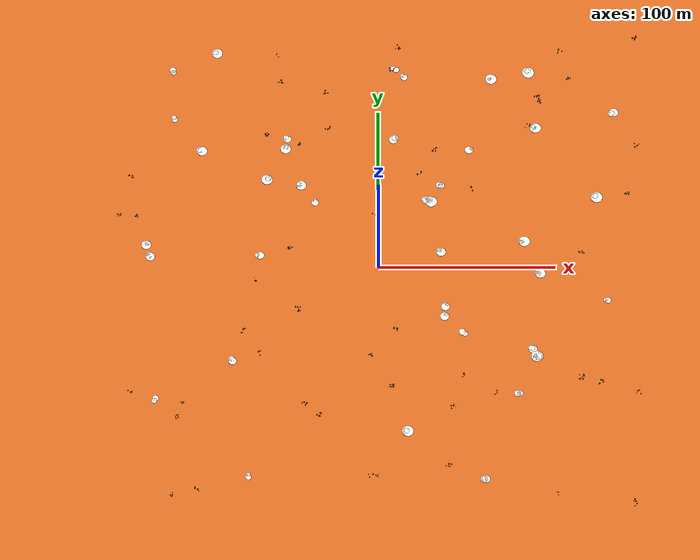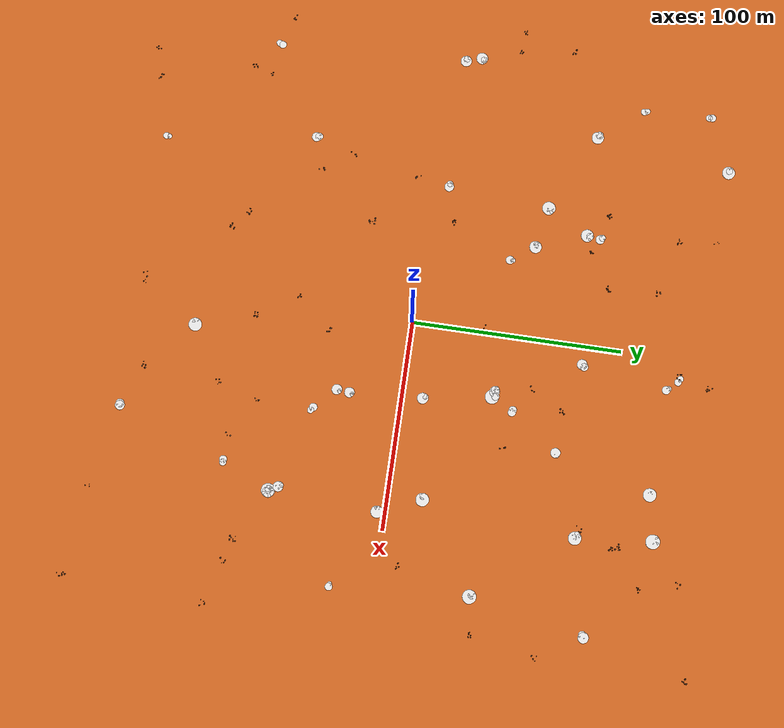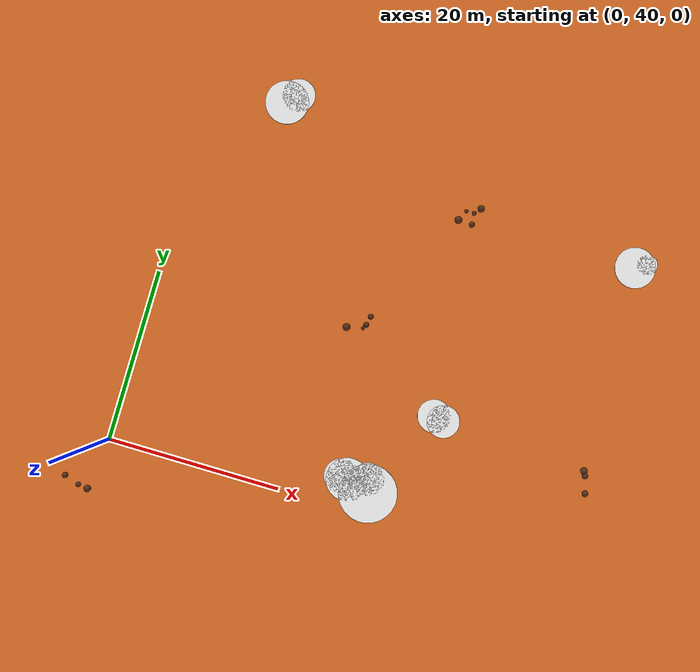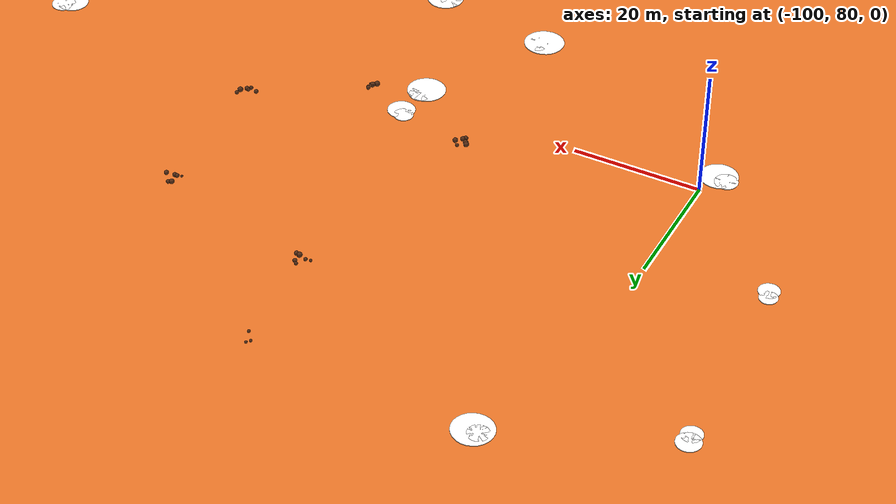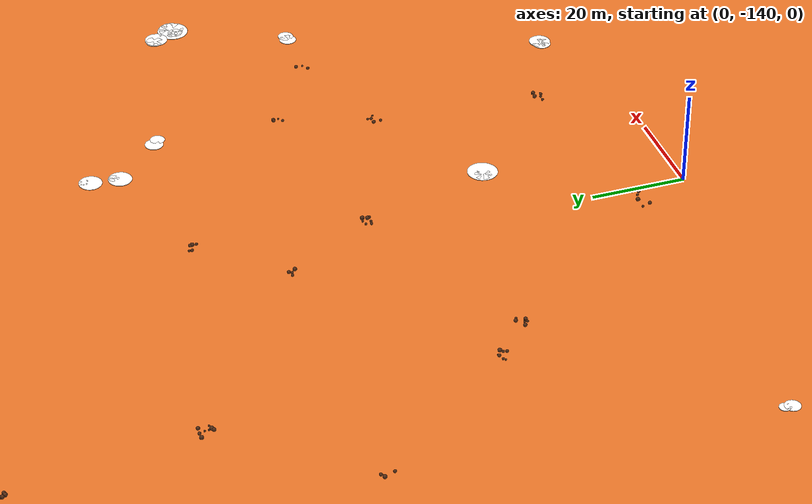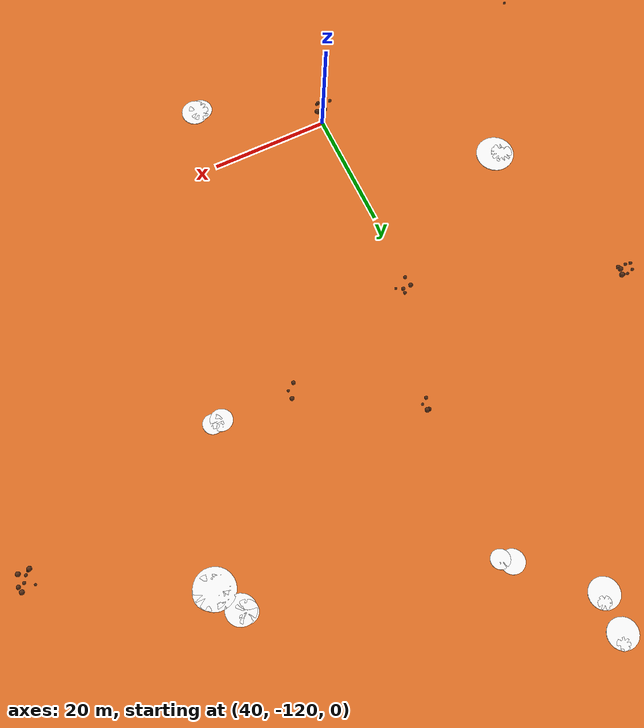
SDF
<?xml version="1.0" ?>
<sdf version="1.5">
  <world name="martian_training_world">
    <!-- Scene Settings optimized for YOLO Training Contrast -->
    <scene>
      <ambient>0.7 0.7 0.7 1.0</ambient>
      <background>0.8 0.4 0.1 1.0</background>
      <shadows>1</shadows>
      <!-- Reduced fog to make bounding box labeling easier from the sky -->
      <fog>
        <color>0.8 0.4 0.1 1.0</color>
        <type>linear</type>
        <start>20</start>
        <end>300</end>
        <density>0.05</density>
      </fog>
    </scene>

    <gravity>0 0 -3.711</gravity>

    <!-- Sun: Balanced to avoid extreme shadows that confuse YOLO -->
    <light name='martian_sun' type='directional'>
      <cast_shadows>1</cast_shadows>
      <pose>0 0 50 0 0 0</pose>
      <diffuse>0.9 0.8 0.7 1</diffuse>
      <specular>0.5 0.5 0.5 1</specular>
      <attenuation>
        <range>1000</range>
        <constant>0.9</constant>
        <linear>0.01</linear>
        <quadratic>0.001</quadratic>
      </attenuation>
      <direction>-0.3 0.3 -0.9</direction>
    </light>

    <!-- Martian Ground: Distinct Orange for YOLO differentiation -->
    <model name='martian_ground'>
      <static>1</static>
      <link name='link'>
        <collision name='collision'>
          <geometry>
            <plane>
              <normal>0 0 1</normal>
              <size>800 800</size>
            </plane>
          </geometry>
          <surface>
            <friction><ode><mu>100</mu><mu2>50</mu2></ode></friction>
          </surface>
        </collision>
        <visual name='visual'>
          <geometry>
            <plane>
              <normal>0 0 1</normal>
              <size>800 800</size>
            </plane>
          </geometry>
          <material>
            <ambient>0.8 0.4 0.1 1</ambient>
            <diffuse>0.9 0.45 0.15 1</diffuse>
            <specular>0.05 0.05 0.05 1</specular>
          </material>
        </visual>
      </link>
    </model>

    <!-- Water Ice (White) -->
    <model name="water_ice_0">
      <static>true</static>
      <pose>35.33 9.98 0.01 0 0 1.15</pose>
      <link name="link">
        <visual name="v"><geometry><cylinder><radius>2.67</radius><length>0.1</length></cylinder></geometry>
          <material><ambient>1.0 1.0 1.0 1</ambient><diffuse>1.0 1.0 1.0 1</diffuse><specular>0.8 0.8 0.8 1</specular></material>
        </visual>
        <visual name="v2"><pose>0.67 1.32 0 0 0 0</pose><geometry><cylinder><radius>1.38</radius><length>0.1</length></cylinder></geometry>
          <material><ambient>1.0 1.0 1.0 1</ambient><diffuse>1.0 1.0 1.0 1</diffuse><specular>0.8 0.8 0.8 1</specular></material>
        </visual>
        <collision name="c"><geometry><cylinder><radius>3.5</radius><length>0.1</length></cylinder></geometry></collision>
      </link>
    </model>

    <!-- Water Ice (White) -->
    <model name="water_ice_1">
      <static>true</static>
      <pose>86.88 126.52 0.01 0 0 0.97</pose>
      <link name="link">
        <visual name="v"><geometry><cylinder><radius>3.48</radius><length>0.1</length></cylinder></geometry>
          <material><ambient>1.0 1.0 1.0 1</ambient><diffuse>1.0 1.0 1.0 1</diffuse><specular>0.8 0.8 0.8 1</specular></material>
        </visual>
        <visual name="v2"><pose>0.70 1.16 0 0 0 0</pose><geometry><cylinder><radius>1.91</radius><length>0.1</length></cylinder></geometry>
          <material><ambient>1.0 1.0 1.0 1</ambient><diffuse>1.0 1.0 1.0 1</diffuse><specular>0.8 0.8 0.8 1</specular></material>
        </visual>
        <collision name="c"><geometry><cylinder><radius>3.5</radius><length>0.1</length></cylinder></geometry></collision>
      </link>
    </model>

    <!-- Water Ice (White) -->
    <model name="water_ice_2">
      <static>true</static>
      <pose>-117.21 96.13 0.01 0 0 1.25</pose>
      <link name="link">
        <visual name="v"><geometry><cylinder><radius>1.63</radius><length>0.1</length></cylinder></geometry>
          <material><ambient>1.0 1.0 1.0 1</ambient><diffuse>1.0 1.0 1.0 1</diffuse><specular>0.8 0.8 0.8 1</specular></material>
        </visual>
        <visual name="v2"><pose>1.20 0.85 0 0 0 0</pose><geometry><cylinder><radius>1.40</radius><length>0.1</length></cylinder></geometry>
          <material><ambient>1.0 1.0 1.0 1</ambient><diffuse>1.0 1.0 1.0 1</diffuse><specular>0.8 0.8 0.8 1</specular></material>
        </visual>
        <collision name="c"><geometry><cylinder><radius>3.5</radius><length>0.1</length></cylinder></geometry></collision>
      </link>
    </model>

    <!-- Water Ice (White) -->
    <model name="water_ice_3">
      <static>true</static>
      <pose>90.48 90.02 0.01 0 0 2.08</pose>
      <link name="link">
        <visual name="v"><geometry><cylinder><radius>3.17</radius><length>0.1</length></cylinder></geometry>
          <material><ambient>1.0 1.0 1.0 1</ambient><diffuse>1.0 1.0 1.0 1</diffuse><specular>0.8 0.8 0.8 1</specular></material>
        </visual>
        <visual name="v2"><pose>1.09 0.96 0 0 0 0</pose><geometry><cylinder><radius>1.96</radius><length>0.1</length></cylinder></geometry>
          <material><ambient>1.0 1.0 1.0 1</ambient><diffuse>1.0 1.0 1.0 1</diffuse><specular>0.8 0.8 0.8 1</specular></material>
        </visual>
        <collision name="c"><geometry><cylinder><radius>3.5</radius><length>0.1</length></cylinder></geometry></collision>
      </link>
    </model>

    <!-- Water Ice (White) -->
    <model name="water_ice_4">
      <static>true</static>
      <pose>88.72 -55.88 0.01 0 0 2.17</pose>
      <link name="link">
        <visual name="v"><geometry><cylinder><radius>3.33</radius><length>0.1</length></cylinder></geometry>
          <material><ambient>1.0 1.0 1.0 1</ambient><diffuse>1.0 1.0 1.0 1</diffuse><specular>0.8 0.8 0.8 1</specular></material>
        </visual>
        <visual name="v2"><pose>0.96 0.76 0 0 0 0</pose><geometry><cylinder><radius>1.20</radius><length>0.1</length></cylinder></geometry>
          <material><ambient>1.0 1.0 1.0 1</ambient><diffuse>1.0 1.0 1.0 1</diffuse><specular>0.8 0.8 0.8 1</specular></material>
        </visual>
        <collision name="c"><geometry><cylinder><radius>3.5</radius><length>0.1</length></cylinder></geometry></collision>
      </link>
    </model>

    <!-- Water Ice (White) -->
    <model name="water_ice_5">
      <static>true</static>
      <pose>-129.81 7.63 0.01 0 0 1.94</pose>
      <link name="link">
        <visual name="v"><geometry><cylinder><radius>2.65</radius><length>0.1</length></cylinder></geometry>
          <material><ambient>1.0 1.0 1.0 1</ambient><diffuse>1.0 1.0 1.0 1</diffuse><specular>0.8 0.8 0.8 1</specular></material>
        </visual>
        <visual name="v2"><pose>0.54 0.91 0 0 0 0</pose><geometry><cylinder><radius>1.65</radius><length>0.1</length></cylinder></geometry>
          <material><ambient>1.0 1.0 1.0 1</ambient><diffuse>1.0 1.0 1.0 1</diffuse><specular>0.8 0.8 0.8 1</specular></material>
        </visual>
        <collision name="c"><geometry><cylinder><radius>3.5</radius><length>0.1</length></cylinder></geometry></collision>
      </link>
    </model>

    <!-- Water Ice (White) -->
    <model name="water_ice_6">
      <static>true</static>
      <pose>35.92 52.68 0.01 0 0 1.99</pose>
      <link name="link">
        <visual name="v"><geometry><cylinder><radius>1.89</radius><length>0.1</length></cylinder></geometry>
          <material><ambient>1.0 1.0 1.0 1</ambient><diffuse>1.0 1.0 1.0 1</diffuse><specular>0.8 0.8 0.8 1</specular></material>
        </visual>
        <visual name="v2"><pose>0.78 0.95 0 0 0 0</pose><geometry><cylinder><radius>1.92</radius><length>0.1</length></cylinder></geometry>
          <material><ambient>1.0 1.0 1.0 1</ambient><diffuse>1.0 1.0 1.0 1</diffuse><specular>0.8 0.8 0.8 1</specular></material>
        </visual>
        <collision name="c"><geometry><cylinder><radius>3.5</radius><length>0.1</length></cylinder></geometry></collision>
      </link>
    </model>

    <!-- Water Ice (White) -->
    <model name="water_ice_7">
      <static>true</static>
      <pose>89.47 -55.72 0.01 0 0 2.50</pose>
      <link name="link">
        <visual name="v"><geometry><cylinder><radius>2.72</radius><length>0.1</length></cylinder></geometry>
          <material><ambient>1.0 1.0 1.0 1</ambient><diffuse>1.0 1.0 1.0 1</diffuse><specular>0.8 0.8 0.8 1</specular></material>
        </visual>
        <visual name="v2"><pose>0.93 1.29 0 0 0 0</pose><geometry><cylinder><radius>1.55</radius><length>0.1</length></cylinder></geometry>
          <material><ambient>1.0 1.0 1.0 1</ambient><diffuse>1.0 1.0 1.0 1</diffuse><specular>0.8 0.8 0.8 1</specular></material>
        </visual>
        <collision name="c"><geometry><cylinder><radius>3.5</radius><length>0.1</length></cylinder></geometry></collision>
      </link>
    </model>

    <!-- Water Ice (White) -->
    <model name="water_ice_8">
      <static>true</static>
      <pose>82.80 16.62 0.01 0 0 2.03</pose>
      <link name="link">
        <visual name="v"><geometry><cylinder><radius>3.20</radius><length>0.1</length></cylinder></geometry>
          <material><ambient>1.0 1.0 1.0 1</ambient><diffuse>1.0 1.0 1.0 1</diffuse><specular>0.8 0.8 0.8 1</specular></material>
        </visual>
        <visual name="v2"><pose>0.71 1.47 0 0 0 0</pose><geometry><cylinder><radius>1.53</radius><length>0.1</length></cylinder></geometry>
          <material><ambient>1.0 1.0 1.0 1</ambient><diffuse>1.0 1.0 1.0 1</diffuse><specular>0.8 0.8 0.8 1</specular></material>
        </visual>
        <collision name="c"><geometry><cylinder><radius>3.5</radius><length>0.1</length></cylinder></geometry></collision>
      </link>
    </model>

    <!-- Water Ice (White) -->
    <model name="water_ice_9">
      <static>true</static>
      <pose>8.53 82.60 0.01 0 0 0.16</pose>
      <link name="link">
        <visual name="v"><geometry><cylinder><radius>2.49</radius><length>0.1</length></cylinder></geometry>
          <material><ambient>1.0 1.0 1.0 1</ambient><diffuse>1.0 1.0 1.0 1</diffuse><specular>0.8 0.8 0.8 1</specular></material>
        </visual>
        <visual name="v2"><pose>1.24 0.96 0 0 0 0</pose><geometry><cylinder><radius>1.90</radius><length>0.1</length></cylinder></geometry>
          <material><ambient>1.0 1.0 1.0 1</ambient><diffuse>1.0 1.0 1.0 1</diffuse><specular>0.8 0.8 0.8 1</specular></material>
        </visual>
        <collision name="c"><geometry><cylinder><radius>3.5</radius><length>0.1</length></cylinder></geometry></collision>
      </link>
    </model>

    <!-- Water Ice (White) -->
    <model name="water_ice_10">
      <static>true</static>
      <pose>91.50 -3.72 0.01 0 0 2.36</pose>
      <link name="link">
        <visual name="v"><geometry><cylinder><radius>2.96</radius><length>0.1</length></cylinder></geometry>
          <material><ambient>1.0 1.0 1.0 1</ambient><diffuse>1.0 1.0 1.0 1</diffuse><specular>0.8 0.8 0.8 1</specular></material>
        </visual>
        <visual name="v2"><pose>0.85 1.06 0 0 0 0</pose><geometry><cylinder><radius>1.57</radius><length>0.1</length></cylinder></geometry>
          <material><ambient>1.0 1.0 1.0 1</ambient><diffuse>1.0 1.0 1.0 1</diffuse><specular>0.8 0.8 0.8 1</specular></material>
        </visual>
        <collision name="c"><geometry><cylinder><radius>3.5</radius><length>0.1</length></cylinder></geometry></collision>
      </link>
    </model>

    <!-- Water Ice (White) -->
    <model name="water_ice_11">
      <static>true</static>
      <pose>-72.81 -129.96 0.01 0 0 0.41</pose>
      <link name="link">
        <visual name="v"><geometry><cylinder><radius>1.62</radius><length>0.1</length></cylinder></geometry>
          <material><ambient>1.0 1.0 1.0 1</ambient><diffuse>1.0 1.0 1.0 1</diffuse><specular>0.8 0.8 0.8 1</specular></material>
        </visual>
        <visual name="v2"><pose>0.67 1.32 0 0 0 0</pose><geometry><cylinder><radius>1.19</radius><length>0.1</length></cylinder></geometry>
          <material><ambient>1.0 1.0 1.0 1</ambient><diffuse>1.0 1.0 1.0 1</diffuse><specular>0.8 0.8 0.8 1</specular></material>
        </visual>
        <collision name="c"><geometry><cylinder><radius>3.5</radius><length>0.1</length></cylinder></geometry></collision>
      </link>
    </model>

    <!-- Water Ice (White) -->
    <model name="water_ice_12">
      <static>true</static>
      <pose>135.80 100.06 0.01 0 0 2.76</pose>
      <link name="link">
        <visual name="v"><geometry><cylinder><radius>2.61</radius><length>0.1</length></cylinder></geometry>
          <material><ambient>1.0 1.0 1.0 1</ambient><diffuse>1.0 1.0 1.0 1</diffuse><specular>0.8 0.8 0.8 1</specular></material>
        </visual>
        <visual name="v2"><pose>0.93 1.11 0 0 0 0</pose><geometry><cylinder><radius>1.88</radius><length>0.1</length></cylinder></geometry>
          <material><ambient>1.0 1.0 1.0 1</ambient><diffuse>1.0 1.0 1.0 1</diffuse><specular>0.8 0.8 0.8 1</specular></material>
        </visual>
        <collision name="c"><geometry><cylinder><radius>3.5</radius><length>0.1</length></cylinder></geometry></collision>
      </link>
    </model>

    <!-- Water Ice (White) -->
    <model name="water_ice_13">
      <static>true</static>
      <pose>129.31 -21.02 0.01 0 0 2.33</pose>
      <link name="link">
        <visual name="v"><geometry><cylinder><radius>1.81</radius><length>0.1</length></cylinder></geometry>
          <material><ambient>1.0 1.0 1.0 1</ambient><diffuse>1.0 1.0 1.0 1</diffuse><specular>0.8 0.8 0.8 1</specular></material>
        </visual>
        <visual name="v2"><pose>1.13 0.85 0 0 0 0</pose><geometry><cylinder><radius>1.07</radius><length>0.1</length></cylinder></geometry>
          <material><ambient>1.0 1.0 1.0 1</ambient><diffuse>1.0 1.0 1.0 1</diffuse><specular>0.8 0.8 0.8 1</specular></material>
        </visual>
        <collision name="c"><geometry><cylinder><radius>3.5</radius><length>0.1</length></cylinder></geometry></collision>
      </link>
    </model>

    <!-- Water Ice (White) -->
    <model name="water_ice_14">
      <static>true</static>
      <pose>-44.27 53.06 0.01 0 0 1.89</pose>
      <link name="link">
        <visual name="v"><geometry><cylinder><radius>2.93</radius><length>0.1</length></cylinder></geometry>
          <material><ambient>1.0 1.0 1.0 1</ambient><diffuse>1.0 1.0 1.0 1</diffuse><specular>0.8 0.8 0.8 1</specular></material>
        </visual>
        <visual name="v2"><pose>0.69 0.98 0 0 0 0</pose><geometry><cylinder><radius>1.61</radius><length>0.1</length></cylinder></geometry>
          <material><ambient>1.0 1.0 1.0 1</ambient><diffuse>1.0 1.0 1.0 1</diffuse><specular>0.8 0.8 0.8 1</specular></material>
        </visual>
        <collision name="c"><geometry><cylinder><radius>3.5</radius><length>0.1</length></cylinder></geometry></collision>
      </link>
    </model>

    <!-- Water Ice (White) -->
    <model name="water_ice_15">
      <static>true</static>
      <pose>15.85 -102.08 0.01 0 0 2.23</pose>
      <link name="link">
        <visual name="v"><geometry><cylinder><radius>3.19</radius><length>0.1</length></cylinder></geometry>
          <material><ambient>1.0 1.0 1.0 1</ambient><diffuse>1.0 1.0 1.0 1</diffuse><specular>0.8 0.8 0.8 1</specular></material>
        </visual>
        <visual name="v2"><pose>0.89 0.69 0 0 0 0</pose><geometry><cylinder><radius>1.76</radius><length>0.1</length></cylinder></geometry>
          <material><ambient>1.0 1.0 1.0 1</ambient><diffuse>1.0 1.0 1.0 1</diffuse><specular>0.8 0.8 0.8 1</specular></material>
        </visual>
        <collision name="c"><geometry><cylinder><radius>3.5</radius><length>0.1</length></cylinder></geometry></collision>
      </link>
    </model>

    <!-- Water Ice (White) -->
    <model name="water_ice_16">
      <static>true</static>
      <pose>37.47 -24.74 0.01 0 0 0.50</pose>
      <link name="link">
        <visual name="v"><geometry><cylinder><radius>2.44</radius><length>0.1</length></cylinder></geometry>
          <material><ambient>1.0 1.0 1.0 1</ambient><diffuse>1.0 1.0 1.0 1</diffuse><specular>0.8 0.8 0.8 1</specular></material>
        </visual>
        <visual name="v2"><pose>1.20 0.82 0 0 0 0</pose><geometry><cylinder><radius>1.03</radius><length>0.1</length></cylinder></geometry>
          <material><ambient>1.0 1.0 1.0 1</ambient><diffuse>1.0 1.0 1.0 1</diffuse><specular>0.8 0.8 0.8 1</specular></material>
        </visual>
        <collision name="c"><geometry><cylinder><radius>3.5</radius><length>0.1</length></cylinder></geometry></collision>
      </link>
    </model>

    <!-- Water Ice (White) -->
    <model name="water_ice_17">
      <static>true</static>
      <pose>29.98 42.39 0.01 0 0 0.96</pose>
      <link name="link">
        <visual name="v"><geometry><cylinder><radius>3.39</radius><length>0.1</length></cylinder></geometry>
          <material><ambient>1.0 1.0 1.0 1</ambient><diffuse>1.0 1.0 1.0 1</diffuse><specular>0.8 0.8 0.8 1</specular></material>
        </visual>
        <visual name="v2"><pose>1.05 1.28 0 0 0 0</pose><geometry><cylinder><radius>1.87</radius><length>0.1</length></cylinder></geometry>
          <material><ambient>1.0 1.0 1.0 1</ambient><diffuse>1.0 1.0 1.0 1</diffuse><specular>0.8 0.8 0.8 1</specular></material>
        </visual>
        <collision name="c"><geometry><cylinder><radius>3.5</radius><length>0.1</length></cylinder></geometry></collision>
      </link>
    </model>

    <!-- Water Ice (White) -->
    <model name="water_ice_18">
      <static>true</static>
      <pose>-82.47 -58.42 0.01 0 0 1.38</pose>
      <link name="link">
        <visual name="v"><geometry><cylinder><radius>2.26</radius><length>0.1</length></cylinder></geometry>
          <material><ambient>1.0 1.0 1.0 1</ambient><diffuse>1.0 1.0 1.0 1</diffuse><specular>0.8 0.8 0.8 1</specular></material>
        </visual>
        <visual name="v2"><pose>1.14 0.64 0 0 0 0</pose><geometry><cylinder><radius>1.82</radius><length>0.1</length></cylinder></geometry>
          <material><ambient>1.0 1.0 1.0 1</ambient><diffuse>1.0 1.0 1.0 1</diffuse><specular>0.8 0.8 0.8 1</specular></material>
        </visual>
        <collision name="c"><geometry><cylinder><radius>3.5</radius><length>0.1</length></cylinder></geometry></collision>
      </link>
    </model>

    <!-- Water Ice (White) -->
    <model name="water_ice_19">
      <static>true</static>
      <pose>78.78 -78.99 0.01 0 0 2.55</pose>
      <link name="link">
        <visual name="v"><geometry><cylinder><radius>1.67</radius><length>0.1</length></cylinder></geometry>
          <material><ambient>1.0 1.0 1.0 1</ambient><diffuse>1.0 1.0 1.0 1</diffuse><specular>0.8 0.8 0.8 1</specular></material>
        </visual>
        <visual name="v2"><pose>1.19 0.84 0 0 0 0</pose><geometry><cylinder><radius>1.84</radius><length>0.1</length></cylinder></geometry>
          <material><ambient>1.0 1.0 1.0 1</ambient><diffuse>1.0 1.0 1.0 1</diffuse><specular>0.8 0.8 0.8 1</specular></material>
        </visual>
        <collision name="c"><geometry><cylinder><radius>3.5</radius><length>0.1</length></cylinder></geometry></collision>
      </link>
    </model>

    <!-- Water Ice (White) -->
    <model name="water_ice_20">
      <static>true</static>
      <pose>-67.44 8.15 0.01 0 0 1.87</pose>
      <link name="link">
        <visual name="v"><geometry><cylinder><radius>2.28</radius><length>0.1</length></cylinder></geometry>
          <material><ambient>1.0 1.0 1.0 1</ambient><diffuse>1.0 1.0 1.0 1</diffuse><specular>0.8 0.8 0.8 1</specular></material>
        </visual>
        <visual name="v2"><pose>0.64 1.36 0 0 0 0</pose><geometry><cylinder><radius>1.50</radius><length>0.1</length></cylinder></geometry>
          <material><ambient>1.0 1.0 1.0 1</ambient><diffuse>1.0 1.0 1.0 1</diffuse><specular>0.8 0.8 0.8 1</specular></material>
        </visual>
        <collision name="c"><geometry><cylinder><radius>3.5</radius><length>0.1</length></cylinder></geometry></collision>
      </link>
    </model>

    <!-- Water Ice (White) -->
    <model name="water_ice_21">
      <static>true</static>
      <pose>-36.36 41.85 0.01 0 0 0.36</pose>
      <link name="link">
        <visual name="v"><geometry><cylinder><radius>1.99</radius><length>0.1</length></cylinder></geometry>
          <material><ambient>1.0 1.0 1.0 1</ambient><diffuse>1.0 1.0 1.0 1</diffuse><specular>0.8 0.8 0.8 1</specular></material>
        </visual>
        <visual name="v2"><pose>0.55 1.29 0 0 0 0</pose><geometry><cylinder><radius>1.21</radius><length>0.1</length></cylinder></geometry>
          <material><ambient>1.0 1.0 1.0 1</ambient><diffuse>1.0 1.0 1.0 1</diffuse><specular>0.8 0.8 0.8 1</specular></material>
        </visual>
        <collision name="c"><geometry><cylinder><radius>3.5</radius><length>0.1</length></cylinder></geometry></collision>
      </link>
    </model>

    <!-- Water Ice (White) -->
    <model name="water_ice_22">
      <static>true</static>
      <pose>10.49 128.68 0.01 0 0 1.82</pose>
      <link name="link">
        <visual name="v"><geometry><cylinder><radius>1.71</radius><length>0.1</length></cylinder></geometry>
          <material><ambient>1.0 1.0 1.0 1</ambient><diffuse>1.0 1.0 1.0 1</diffuse><specular>0.8 0.8 0.8 1</specular></material>
        </visual>
        <visual name="v2"><pose>1.36 1.45 0 0 0 0</pose><geometry><cylinder><radius>1.51</radius><length>0.1</length></cylinder></geometry>
          <material><ambient>1.0 1.0 1.0 1</ambient><diffuse>1.0 1.0 1.0 1</diffuse><specular>0.8 0.8 0.8 1</specular></material>
        </visual>
        <collision name="c"><geometry><cylinder><radius>3.5</radius><length>0.1</length></cylinder></geometry></collision>
      </link>
    </model>

    <!-- Water Ice (White) -->
    <model name="water_ice_23">
      <static>true</static>
      <pose>27.29 43.27 0.01 0 0 2.01</pose>
      <link name="link">
        <visual name="v"><geometry><cylinder><radius>2.49</radius><length>0.1</length></cylinder></geometry>
          <material><ambient>1.0 1.0 1.0 1</ambient><diffuse>1.0 1.0 1.0 1</diffuse><specular>0.8 0.8 0.8 1</specular></material>
        </visual>
        <visual name="v2"><pose>0.52 0.65 0 0 0 0</pose><geometry><cylinder><radius>1.98</radius><length>0.1</length></cylinder></geometry>
          <material><ambient>1.0 1.0 1.0 1</ambient><diffuse>1.0 1.0 1.0 1</diffuse><specular>0.8 0.8 0.8 1</specular></material>
        </visual>
        <collision name="c"><geometry><cylinder><radius>3.5</radius><length>0.1</length></cylinder></geometry></collision>
      </link>
    </model>

    <!-- Water Ice (White) -->
    <model name="water_ice_24">
      <static>true</static>
      <pose>124.56 44.79 0.01 0 0 1.93</pose>
      <link name="link">
        <visual name="v"><geometry><cylinder><radius>3.36</radius><length>0.1</length></cylinder></geometry>
          <material><ambient>1.0 1.0 1.0 1</ambient><diffuse>1.0 1.0 1.0 1</diffuse><specular>0.8 0.8 0.8 1</specular></material>
        </visual>
        <visual name="v2"><pose>1.24 0.52 0 0 0 0</pose><geometry><cylinder><radius>1.79</radius><length>0.1</length></cylinder></geometry>
          <material><ambient>1.0 1.0 1.0 1</ambient><diffuse>1.0 1.0 1.0 1</diffuse><specular>0.8 0.8 0.8 1</specular></material>
        </visual>
        <collision name="c"><geometry><cylinder><radius>3.5</radius><length>0.1</length></cylinder></geometry></collision>
      </link>
    </model>

    <!-- Water Ice (White) -->
    <model name="water_ice_25">
      <static>true</static>
      <pose>-101.30 75.55 0.01 0 0 2.03</pose>
      <link name="link">
        <visual name="v"><geometry><cylinder><radius>2.92</radius><length>0.1</length></cylinder></geometry>
          <material><ambient>1.0 1.0 1.0 1</ambient><diffuse>1.0 1.0 1.0 1</diffuse><specular>0.8 0.8 0.8 1</specular></material>
        </visual>
        <visual name="v2"><pose>1.30 0.96 0 0 0 0</pose><geometry><cylinder><radius>1.81</radius><length>0.1</length></cylinder></geometry>
          <material><ambient>1.0 1.0 1.0 1</ambient><diffuse>1.0 1.0 1.0 1</diffuse><specular>0.8 0.8 0.8 1</specular></material>
        </visual>
        <collision name="c"><geometry><cylinder><radius>3.5</radius><length>0.1</length></cylinder></geometry></collision>
      </link>
    </model>

    <!-- Water Ice (White) -->
    <model name="water_ice_26">
      <static>true</static>
      <pose>51.97 75.70 0.01 0 0 0.08</pose>
      <link name="link">
        <visual name="v"><geometry><cylinder><radius>2.35</radius><length>0.1</length></cylinder></geometry>
          <material><ambient>1.0 1.0 1.0 1</ambient><diffuse>1.0 1.0 1.0 1</diffuse><specular>0.8 0.8 0.8 1</specular></material>
        </visual>
        <visual name="v2"><pose>1.29 0.60 0 0 0 0</pose><geometry><cylinder><radius>1.17</radius><length>0.1</length></cylinder></geometry>
          <material><ambient>1.0 1.0 1.0 1</ambient><diffuse>1.0 1.0 1.0 1</diffuse><specular>0.8 0.8 0.8 1</specular></material>
        </visual>
        <collision name="c"><geometry><cylinder><radius>3.5</radius><length>0.1</length></cylinder></geometry></collision>
      </link>
    </model>

    <!-- Water Ice (White) -->
    <model name="water_ice_27">
      <static>true</static>
      <pose>65.33 122.28 0.01 0 0 1.98</pose>
      <link name="link">
        <visual name="v"><geometry><cylinder><radius>3.22</radius><length>0.1</length></cylinder></geometry>
          <material><ambient>1.0 1.0 1.0 1</ambient><diffuse>1.0 1.0 1.0 1</diffuse><specular>0.8 0.8 0.8 1</specular></material>
        </visual>
        <visual name="v2"><pose>0.66 0.70 0 0 0 0</pose><geometry><cylinder><radius>1.08</radius><length>0.1</length></cylinder></geometry>
          <material><ambient>1.0 1.0 1.0 1</ambient><diffuse>1.0 1.0 1.0 1</diffuse><specular>0.8 0.8 0.8 1</specular></material>
        </visual>
        <collision name="c"><geometry><cylinder><radius>3.5</radius><length>0.1</length></cylinder></geometry></collision>
      </link>
    </model>

    <!-- Water Ice (White) -->
    <model name="water_ice_28">
      <static>true</static>
      <pose>15.01 123.61 0.01 0 0 1.81</pose>
      <link name="link">
        <visual name="v"><geometry><cylinder><radius>1.99</radius><length>0.1</length></cylinder></geometry>
          <material><ambient>1.0 1.0 1.0 1</ambient><diffuse>1.0 1.0 1.0 1</diffuse><specular>0.8 0.8 0.8 1</specular></material>
        </visual>
        <visual name="v2"><pose>1.41 0.56 0 0 0 0</pose><geometry><cylinder><radius>1.23</radius><length>0.1</length></cylinder></geometry>
          <material><ambient>1.0 1.0 1.0 1</ambient><diffuse>1.0 1.0 1.0 1</diffuse><specular>0.8 0.8 0.8 1</specular></material>
        </visual>
        <collision name="c"><geometry><cylinder><radius>3.5</radius><length>0.1</length></cylinder></geometry></collision>
      </link>
    </model>

    <!-- Water Ice (White) -->
    <model name="water_ice_29">
      <static>true</static>
      <pose>86.43 -51.51 0.01 0 0 1.73</pose>
      <link name="link">
        <visual name="v"><geometry><cylinder><radius>2.45</radius><length>0.1</length></cylinder></geometry>
          <material><ambient>1.0 1.0 1.0 1</ambient><diffuse>1.0 1.0 1.0 1</diffuse><specular>0.8 0.8 0.8 1</specular></material>
        </visual>
        <visual name="v2"><pose>0.69 0.57 0 0 0 0</pose><geometry><cylinder><radius>1.85</radius><length>0.1</length></cylinder></geometry>
          <material><ambient>1.0 1.0 1.0 1</ambient><diffuse>1.0 1.0 1.0 1</diffuse><specular>0.8 0.8 0.8 1</specular></material>
        </visual>
        <collision name="c"><geometry><cylinder><radius>3.5</radius><length>0.1</length></cylinder></geometry></collision>
      </link>
    </model>

    <!-- Water Ice (White) -->
    <model name="water_ice_30">
      <static>true</static>
      <pose>48.40 -41.73 0.01 0 0 1.82</pose>
      <link name="link">
        <visual name="v"><geometry><cylinder><radius>1.56</radius><length>0.1</length></cylinder></geometry>
          <material><ambient>1.0 1.0 1.0 1</ambient><diffuse>1.0 1.0 1.0 1</diffuse><specular>0.8 0.8 0.8 1</specular></material>
        </visual>
        <visual name="v2"><pose>1.44 1.18 0 0 0 0</pose><geometry><cylinder><radius>1.95</radius><length>0.1</length></cylinder></geometry>
          <material><ambient>1.0 1.0 1.0 1</ambient><diffuse>1.0 1.0 1.0 1</diffuse><specular>0.8 0.8 0.8 1</specular></material>
        </visual>
        <collision name="c"><geometry><cylinder><radius>3.5</radius><length>0.1</length></cylinder></geometry></collision>
      </link>
    </model>

    <!-- Water Ice (White) -->
    <model name="water_ice_31">
      <static>true</static>
      <pose>-132.24 15.06 0.01 0 0 0.36</pose>
      <link name="link">
        <visual name="v"><geometry><cylinder><radius>2.80</radius><length>0.1</length></cylinder></geometry>
          <material><ambient>1.0 1.0 1.0 1</ambient><diffuse>1.0 1.0 1.0 1</diffuse><specular>0.8 0.8 0.8 1</specular></material>
        </visual>
        <visual name="v2"><pose>0.90 0.78 0 0 0 0</pose><geometry><cylinder><radius>1.56</radius><length>0.1</length></cylinder></geometry>
          <material><ambient>1.0 1.0 1.0 1</ambient><diffuse>1.0 1.0 1.0 1</diffuse><specular>0.8 0.8 0.8 1</specular></material>
        </visual>
        <collision name="c"><geometry><cylinder><radius>3.5</radius><length>0.1</length></cylinder></geometry></collision>
      </link>
    </model>

    <!-- Water Ice (White) -->
    <model name="water_ice_32">
      <static>true</static>
      <pose>-63.88 56.86 0.01 0 0 0.02</pose>
      <link name="link">
        <visual name="v"><geometry><cylinder><radius>3.20</radius><length>0.1</length></cylinder></geometry>
          <material><ambient>1.0 1.0 1.0 1</ambient><diffuse>1.0 1.0 1.0 1</diffuse><specular>0.8 0.8 0.8 1</specular></material>
        </visual>
        <visual name="v2"><pose>0.80 0.87 0 0 0 0</pose><geometry><cylinder><radius>1.77</radius><length>0.1</length></cylinder></geometry>
          <material><ambient>1.0 1.0 1.0 1</ambient><diffuse>1.0 1.0 1.0 1</diffuse><specular>0.8 0.8 0.8 1</specular></material>
        </visual>
        <collision name="c"><geometry><cylinder><radius>3.5</radius><length>0.1</length></cylinder></geometry></collision>
      </link>
    </model>

    <!-- Water Ice (White) -->
    <model name="water_ice_33">
      <static>true</static>
      <pose>-53.28 76.83 0.01 0 0 0.18</pose>
      <link name="link">
        <visual name="v"><geometry><cylinder><radius>3.02</radius><length>0.1</length></cylinder></geometry>
          <material><ambient>1.0 1.0 1.0 1</ambient><diffuse>1.0 1.0 1.0 1</diffuse><specular>0.8 0.8 0.8 1</specular></material>
        </visual>
        <visual name="v2"><pose>0.55 1.26 0 0 0 0</pose><geometry><cylinder><radius>1.80</radius><length>0.1</length></cylinder></geometry>
          <material><ambient>1.0 1.0 1.0 1</ambient><diffuse>1.0 1.0 1.0 1</diffuse><specular>0.8 0.8 0.8 1</specular></material>
        </visual>
        <collision name="c"><geometry><cylinder><radius>3.5</radius><length>0.1</length></cylinder></geometry></collision>
      </link>
    </model>

    <!-- Water Ice (White) -->
    <model name="water_ice_34">
      <static>true</static>
      <pose>36.95 -30.84 0.01 0 0 0.55</pose>
      <link name="link">
        <visual name="v"><geometry><cylinder><radius>2.49</radius><length>0.1</length></cylinder></geometry>
          <material><ambient>1.0 1.0 1.0 1</ambient><diffuse>1.0 1.0 1.0 1</diffuse><specular>0.8 0.8 0.8 1</specular></material>
        </visual>
        <visual name="v2"><pose>1.17 0.68 0 0 0 0</pose><geometry><cylinder><radius>1.07</radius><length>0.1</length></cylinder></geometry>
          <material><ambient>1.0 1.0 1.0 1</ambient><diffuse>1.0 1.0 1.0 1</diffuse><specular>0.8 0.8 0.8 1</specular></material>
        </visual>
        <collision name="c"><geometry><cylinder><radius>3.5</radius><length>0.1</length></cylinder></geometry></collision>
      </link>
    </model>

    <!-- Water Ice (White) -->
    <model name="water_ice_35">
      <static>true</static>
      <pose>-93.28 139.91 0.01 0 0 2.01</pose>
      <link name="link">
        <visual name="v"><geometry><cylinder><radius>3.07</radius><length>0.1</length></cylinder></geometry>
          <material><ambient>1.0 1.0 1.0 1</ambient><diffuse>1.0 1.0 1.0 1</diffuse><specular>0.8 0.8 0.8 1</specular></material>
        </visual>
        <visual name="v2"><pose>0.66 0.72 0 0 0 0</pose><geometry><cylinder><radius>1.60</radius><length>0.1</length></cylinder></geometry>
          <material><ambient>1.0 1.0 1.0 1</ambient><diffuse>1.0 1.0 1.0 1</diffuse><specular>0.8 0.8 0.8 1</specular></material>
        </visual>
        <collision name="c"><geometry><cylinder><radius>3.5</radius><length>0.1</length></cylinder></geometry></collision>
      </link>
    </model>

    <!-- Water Ice (White) -->
    <model name="water_ice_36">
      <static>true</static>
      <pose>-125.87 -82.95 0.01 0 0 0.58</pose>
      <link name="link">
        <visual name="v"><geometry><cylinder><radius>1.54</radius><length>0.1</length></cylinder></geometry>
          <material><ambient>1.0 1.0 1.0 1</ambient><diffuse>1.0 1.0 1.0 1</diffuse><specular>0.8 0.8 0.8 1</specular></material>
        </visual>
        <visual name="v2"><pose>1.46 1.02 0 0 0 0</pose><geometry><cylinder><radius>1.76</radius><length>0.1</length></cylinder></geometry>
          <material><ambient>1.0 1.0 1.0 1</ambient><diffuse>1.0 1.0 1.0 1</diffuse><specular>0.8 0.8 0.8 1</specular></material>
        </visual>
        <collision name="c"><geometry><cylinder><radius>3.5</radius><length>0.1</length></cylinder></geometry></collision>
      </link>
    </model>

    <!-- Water Ice (White) -->
    <model name="water_ice_37">
      <static>true</static>
      <pose>-118.71 127.32 0.01 0 0 1.01</pose>
      <link name="link">
        <visual name="v"><geometry><cylinder><radius>1.60</radius><length>0.1</length></cylinder></geometry>
          <material><ambient>1.0 1.0 1.0 1</ambient><diffuse>1.0 1.0 1.0 1</diffuse><specular>0.8 0.8 0.8 1</specular></material>
        </visual>
        <visual name="v2"><pose>1.21 0.99 0 0 0 0</pose><geometry><cylinder><radius>1.83</radius><length>0.1</length></cylinder></geometry>
          <material><ambient>1.0 1.0 1.0 1</ambient><diffuse>1.0 1.0 1.0 1</diffuse><specular>0.8 0.8 0.8 1</specular></material>
        </visual>
        <collision name="c"><geometry><cylinder><radius>3.5</radius><length>0.1</length></cylinder></geometry></collision>
      </link>
    </model>

    <!-- Water Ice (White) -->
    <model name="water_ice_38">
      <static>true</static>
      <pose>-52.27 83.16 0.01 0 0 1.84</pose>
      <link name="link">
        <visual name="v"><geometry><cylinder><radius>2.16</radius><length>0.1</length></cylinder></geometry>
          <material><ambient>1.0 1.0 1.0 1</ambient><diffuse>1.0 1.0 1.0 1</diffuse><specular>0.8 0.8 0.8 1</specular></material>
        </visual>
        <visual name="v2"><pose>1.20 0.60 0 0 0 0</pose><geometry><cylinder><radius>1.54</radius><length>0.1</length></cylinder></geometry>
          <material><ambient>1.0 1.0 1.0 1</ambient><diffuse>1.0 1.0 1.0 1</diffuse><specular>0.8 0.8 0.8 1</specular></material>
        </visual>
        <collision name="c"><geometry><cylinder><radius>3.5</radius><length>0.1</length></cylinder></geometry></collision>
      </link>
    </model>

    <!-- Water Ice (White) -->
    <model name="water_ice_39">
      <static>true</static>
      <pose>59.04 -131.42 0.01 0 0 2.16</pose>
      <link name="link">
        <visual name="v"><geometry><cylinder><radius>2.30</radius><length>0.1</length></cylinder></geometry>
          <material><ambient>1.0 1.0 1.0 1</ambient><diffuse>1.0 1.0 1.0 1</diffuse><specular>0.8 0.8 0.8 1</specular></material>
        </visual>
        <visual name="v2"><pose>0.54 0.90 0 0 0 0</pose><geometry><cylinder><radius>1.98</radius><length>0.1</length></cylinder></geometry>
          <material><ambient>1.0 1.0 1.0 1</ambient><diffuse>1.0 1.0 1.0 1</diffuse><specular>0.8 0.8 0.8 1</specular></material>
        </visual>
        <collision name="c"><geometry><cylinder><radius>3.5</radius><length>0.1</length></cylinder></geometry></collision>
      </link>
    </model>

    <!-- Regolith (Dark Brown) -->
    <model name="regolith_field_0">
      <static>true</static>
      <pose>-137.74 34.38 0 0 0 1.36</pose>
      <link name="link">

        <visual name="v0"><pose>-1.25 -0.54 0.17 0 0 0</pose><geometry><sphere><radius>0.33</radius></sphere></geometry>
          <material><ambient>0.3 0.15 0.05 1</ambient><diffuse>0.35 0.18 0.08 1</diffuse></material>
        </visual>
        <collision name="c0"><pose>-1.25 -0.54 0.17 0 0 0</pose><geometry><sphere><radius>0.33</radius></sphere></geometry></collision>

        <visual name="v1"><pose>-0.16 0.03 0.13 0 0 0</pose><geometry><sphere><radius>0.25</radius></sphere></geometry>
          <material><ambient>0.3 0.15 0.05 1</ambient><diffuse>0.35 0.18 0.08 1</diffuse></material>
        </visual>
        <collision name="c1"><pose>-0.16 0.03 0.13 0 0 0</pose><geometry><sphere><radius>0.25</radius></sphere></geometry></collision>

        <visual name="v2"><pose>-0.12 0.26 0.21 0 0 0</pose><geometry><sphere><radius>0.41</radius></sphere></geometry>
          <material><ambient>0.3 0.15 0.05 1</ambient><diffuse>0.35 0.18 0.08 1</diffuse></material>
        </visual>
        <collision name="c2"><pose>-0.12 0.26 0.21 0 0 0</pose><geometry><sphere><radius>0.41</radius></sphere></geometry></collision>

        <visual name="v3"><pose>-0.41 -0.38 0.12 0 0 0</pose><geometry><sphere><radius>0.24</radius></sphere></geometry>
          <material><ambient>0.3 0.15 0.05 1</ambient><diffuse>0.35 0.18 0.08 1</diffuse></material>
        </visual>
        <collision name="c3"><pose>-0.41 -0.38 0.12 0 0 0</pose><geometry><sphere><radius>0.24</radius></sphere></geometry></collision>

        <visual name="v4"><pose>-1.18 0.91 0.15 0 0 0</pose><geometry><sphere><radius>0.30</radius></sphere></geometry>
          <material><ambient>0.3 0.15 0.05 1</ambient><diffuse>0.35 0.18 0.08 1</diffuse></material>
        </visual>
        <collision name="c4"><pose>-1.18 0.91 0.15 0 0 0</pose><geometry><sphere><radius>0.30</radius></sphere></geometry></collision>

        <visual name="v5"><pose>-1.09 0.49 0.13 0 0 0</pose><geometry><sphere><radius>0.27</radius></sphere></geometry>
          <material><ambient>0.3 0.15 0.05 1</ambient><diffuse>0.35 0.18 0.08 1</diffuse></material>
        </visual>
        <collision name="c5"><pose>-1.09 0.49 0.13 0 0 0</pose><geometry><sphere><radius>0.27</radius></sphere></geometry></collision>

      </link>
    </model>

    <!-- Regolith (Dark Brown) -->
    <model name="regolith_field_1">
      <static>true</static>
      <pose>-4.71 -128.98 0 0 0 1.94</pose>
      <link name="link">

        <visual name="v0"><pose>0.97 1.13 0.13 0 0 0</pose><geometry><sphere><radius>0.27</radius></sphere></geometry>
          <material><ambient>0.3 0.15 0.05 1</ambient><diffuse>0.35 0.18 0.08 1</diffuse></material>
        </visual>
        <collision name="c0"><pose>0.97 1.13 0.13 0 0 0</pose><geometry><sphere><radius>0.27</radius></sphere></geometry></collision>

        <visual name="v1"><pose>0.12 -1.24 0.22 0 0 0</pose><geometry><sphere><radius>0.43</radius></sphere></geometry>
          <material><ambient>0.3 0.15 0.05 1</ambient><diffuse>0.35 0.18 0.08 1</diffuse></material>
        </visual>
        <collision name="c1"><pose>0.12 -1.24 0.22 0 0 0</pose><geometry><sphere><radius>0.43</radius></sphere></geometry></collision>

        <visual name="v2"><pose>-0.05 -1.05 0.11 0 0 0</pose><geometry><sphere><radius>0.23</radius></sphere></geometry>
          <material><ambient>0.3 0.15 0.05 1</ambient><diffuse>0.35 0.18 0.08 1</diffuse></material>
        </visual>
        <collision name="c2"><pose>-0.05 -1.05 0.11 0 0 0</pose><geometry><sphere><radius>0.23</radius></sphere></geometry></collision>

        <visual name="v3"><pose>-0.89 1.20 0.19 0 0 0</pose><geometry><sphere><radius>0.38</radius></sphere></geometry>
          <material><ambient>0.3 0.15 0.05 1</ambient><diffuse>0.35 0.18 0.08 1</diffuse></material>
        </visual>
        <collision name="c3"><pose>-0.89 1.20 0.19 0 0 0</pose><geometry><sphere><radius>0.38</radius></sphere></geometry></collision>

      </link>
    </model>

    <!-- Regolith (Dark Brown) -->
    <model name="regolith_field_2">
      <static>true</static>
      <pose>-101.07 -136.88 0 0 0 0.01</pose>
      <link name="link">

        <visual name="v0"><pose>0.86 -1.13 0.12 0 0 0</pose><geometry><sphere><radius>0.25</radius></sphere></geometry>
          <material><ambient>0.3 0.15 0.05 1</ambient><diffuse>0.35 0.18 0.08 1</diffuse></material>
        </visual>
        <collision name="c0"><pose>0.86 -1.13 0.12 0 0 0</pose><geometry><sphere><radius>0.25</radius></sphere></geometry></collision>

        <visual name="v1"><pose>-1.31 0.05 0.18 0 0 0</pose><geometry><sphere><radius>0.36</radius></sphere></geometry>
          <material><ambient>0.3 0.15 0.05 1</ambient><diffuse>0.35 0.18 0.08 1</diffuse></material>
        </visual>
        <collision name="c1"><pose>-1.31 0.05 0.18 0 0 0</pose><geometry><sphere><radius>0.36</radius></sphere></geometry></collision>

        <visual name="v2"><pose>0.22 -0.36 0.22 0 0 0</pose><geometry><sphere><radius>0.44</radius></sphere></geometry>
          <material><ambient>0.3 0.15 0.05 1</ambient><diffuse>0.35 0.18 0.08 1</diffuse></material>
        </visual>
        <collision name="c2"><pose>0.22 -0.36 0.22 0 0 0</pose><geometry><sphere><radius>0.44</radius></sphere></geometry></collision>

        <visual name="v3"><pose>-1.23 0.94 0.19 0 0 0</pose><geometry><sphere><radius>0.38</radius></sphere></geometry>
          <material><ambient>0.3 0.15 0.05 1</ambient><diffuse>0.35 0.18 0.08 1</diffuse></material>
        </visual>
        <collision name="c3"><pose>-1.23 0.94 0.19 0 0 0</pose><geometry><sphere><radius>0.38</radius></sphere></geometry></collision>

      </link>
    </model>

    <!-- Regolith (Dark Brown) -->
    <model name="regolith_field_3">
      <static>true</static>
      <pose>-41.89 -85.03 0 0 0 2.20</pose>
      <link name="link">

        <visual name="v0"><pose>1.23 0.67 0.13 0 0 0</pose><geometry><sphere><radius>0.26</radius></sphere></geometry>
          <material><ambient>0.3 0.15 0.05 1</ambient><diffuse>0.35 0.18 0.08 1</diffuse></material>
        </visual>
        <collision name="c0"><pose>1.23 0.67 0.13 0 0 0</pose><geometry><sphere><radius>0.26</radius></sphere></geometry></collision>

        <visual name="v1"><pose>-0.61 -0.55 0.14 0 0 0</pose><geometry><sphere><radius>0.28</radius></sphere></geometry>
          <material><ambient>0.3 0.15 0.05 1</ambient><diffuse>0.35 0.18 0.08 1</diffuse></material>
        </visual>
        <collision name="c1"><pose>-0.61 -0.55 0.14 0 0 0</pose><geometry><sphere><radius>0.28</radius></sphere></geometry></collision>

        <visual name="v2"><pose>-0.63 -1.37 0.15 0 0 0</pose><geometry><sphere><radius>0.31</radius></sphere></geometry>
          <material><ambient>0.3 0.15 0.05 1</ambient><diffuse>0.35 0.18 0.08 1</diffuse></material>
        </visual>
        <collision name="c2"><pose>-0.63 -1.37 0.15 0 0 0</pose><geometry><sphere><radius>0.31</radius></sphere></geometry></collision>

        <visual name="v3"><pose>-0.48 -1.23 0.21 0 0 0</pose><geometry><sphere><radius>0.43</radius></sphere></geometry>
          <material><ambient>0.3 0.15 0.05 1</ambient><diffuse>0.35 0.18 0.08 1</diffuse></material>
        </visual>
        <collision name="c3"><pose>-0.48 -1.23 0.21 0 0 0</pose><geometry><sphere><radius>0.43</radius></sphere></geometry></collision>

        <visual name="v4"><pose>0.78 -0.69 0.13 0 0 0</pose><geometry><sphere><radius>0.27</radius></sphere></geometry>
          <material><ambient>0.3 0.15 0.05 1</ambient><diffuse>0.35 0.18 0.08 1</diffuse></material>
        </visual>
        <collision name="c4"><pose>0.78 -0.69 0.13 0 0 0</pose><geometry><sphere><radius>0.27</radius></sphere></geometry></collision>

        <visual name="v5"><pose>1.13 1.16 0.11 0 0 0</pose><geometry><sphere><radius>0.21</radius></sphere></geometry>
          <material><ambient>0.3 0.15 0.05 1</ambient><diffuse>0.35 0.18 0.08 1</diffuse></material>
        </visual>
        <collision name="c5"><pose>1.13 1.16 0.11 0 0 0</pose><geometry><sphere><radius>0.21</radius></sphere></geometry></collision>

        <visual name="v6"><pose>-1.08 -0.01 0.16 0 0 0</pose><geometry><sphere><radius>0.32</radius></sphere></geometry>
          <material><ambient>0.3 0.15 0.05 1</ambient><diffuse>0.35 0.18 0.08 1</diffuse></material>
        </visual>
        <collision name="c6"><pose>-1.08 -0.01 0.16 0 0 0</pose><geometry><sphere><radius>0.32</radius></sphere></geometry></collision>

        <visual name="v7"><pose>0.88 -0.47 0.18 0 0 0</pose><geometry><sphere><radius>0.35</radius></sphere></geometry>
          <material><ambient>0.3 0.15 0.05 1</ambient><diffuse>0.35 0.18 0.08 1</diffuse></material>
        </visual>
        <collision name="c7"><pose>0.88 -0.47 0.18 0 0 0</pose><geometry><sphere><radius>0.35</radius></sphere></geometry></collision>

      </link>
    </model>

    <!-- Regolith (Dark Brown) -->
    <model name="regolith_field_4">
      <static>true</static>
      <pose>141.95 47.59 0 0 0 1.38</pose>
      <link name="link">

        <visual name="v0"><pose>-0.93 0.58 0.15 0 0 0</pose><geometry><sphere><radius>0.30</radius></sphere></geometry>
          <material><ambient>0.3 0.15 0.05 1</ambient><diffuse>0.35 0.18 0.08 1</diffuse></material>
        </visual>
        <collision name="c0"><pose>-0.93 0.58 0.15 0 0 0</pose><geometry><sphere><radius>0.30</radius></sphere></geometry></collision>

        <visual name="v1"><pose>-0.57 0.88 0.16 0 0 0</pose><geometry><sphere><radius>0.32</radius></sphere></geometry>
          <material><ambient>0.3 0.15 0.05 1</ambient><diffuse>0.35 0.18 0.08 1</diffuse></material>
        </visual>
        <collision name="c1"><pose>-0.57 0.88 0.16 0 0 0</pose><geometry><sphere><radius>0.32</radius></sphere></geometry></collision>

        <visual name="v2"><pose>0.34 -0.28 0.16 0 0 0</pose><geometry><sphere><radius>0.31</radius></sphere></geometry>
          <material><ambient>0.3 0.15 0.05 1</ambient><diffuse>0.35 0.18 0.08 1</diffuse></material>
        </visual>
        <collision name="c2"><pose>0.34 -0.28 0.16 0 0 0</pose><geometry><sphere><radius>0.31</radius></sphere></geometry></collision>

        <visual name="v3"><pose>0.65 -1.12 0.15 0 0 0</pose><geometry><sphere><radius>0.29</radius></sphere></geometry>
          <material><ambient>0.3 0.15 0.05 1</ambient><diffuse>0.35 0.18 0.08 1</diffuse></material>
        </visual>
        <collision name="c3"><pose>0.65 -1.12 0.15 0 0 0</pose><geometry><sphere><radius>0.29</radius></sphere></geometry></collision>

        <visual name="v4"><pose>-0.34 -1.27 0.14 0 0 0</pose><geometry><sphere><radius>0.28</radius></sphere></geometry>
          <material><ambient>0.3 0.15 0.05 1</ambient><diffuse>0.35 0.18 0.08 1</diffuse></material>
        </visual>
        <collision name="c4"><pose>-0.34 -1.27 0.14 0 0 0</pose><geometry><sphere><radius>0.28</radius></sphere></geometry></collision>

        <visual name="v5"><pose>-0.75 0.20 0.19 0 0 0</pose><geometry><sphere><radius>0.38</radius></sphere></geometry>
          <material><ambient>0.3 0.15 0.05 1</ambient><diffuse>0.35 0.18 0.08 1</diffuse></material>
        </visual>
        <collision name="c5"><pose>-0.75 0.20 0.19 0 0 0</pose><geometry><sphere><radius>0.38</radius></sphere></geometry></collision>

        <visual name="v6"><pose>-0.75 -1.20 0.12 0 0 0</pose><geometry><sphere><radius>0.25</radius></sphere></geometry>
          <material><ambient>0.3 0.15 0.05 1</ambient><diffuse>0.35 0.18 0.08 1</diffuse></material>
        </visual>
        <collision name="c6"><pose>-0.75 -1.20 0.12 0 0 0</pose><geometry><sphere><radius>0.25</radius></sphere></geometry></collision>

      </link>
    </model>

    <!-- Regolith (Dark Brown) -->
    <model name="regolith_field_5">
      <static>true</static>
      <pose>-45.59 -26.13 0 0 0 1.61</pose>
      <link name="link">

        <visual name="v0"><pose>-1.04 -0.34 0.22 0 0 0</pose><geometry><sphere><radius>0.44</radius></sphere></geometry>
          <material><ambient>0.3 0.15 0.05 1</ambient><diffuse>0.35 0.18 0.08 1</diffuse></material>
        </visual>
        <collision name="c0"><pose>-1.04 -0.34 0.22 0 0 0</pose><geometry><sphere><radius>0.44</radius></sphere></geometry></collision>

        <visual name="v1"><pose>-0.46 -0.20 0.10 0 0 0</pose><geometry><sphere><radius>0.20</radius></sphere></geometry>
          <material><ambient>0.3 0.15 0.05 1</ambient><diffuse>0.35 0.18 0.08 1</diffuse></material>
        </visual>
        <collision name="c1"><pose>-0.46 -0.20 0.10 0 0 0</pose><geometry><sphere><radius>0.20</radius></sphere></geometry></collision>

        <visual name="v2"><pose>1.31 -1.22 0.19 0 0 0</pose><geometry><sphere><radius>0.38</radius></sphere></geometry>
          <material><ambient>0.3 0.15 0.05 1</ambient><diffuse>0.35 0.18 0.08 1</diffuse></material>
        </visual>
        <collision name="c2"><pose>1.31 -1.22 0.19 0 0 0</pose><geometry><sphere><radius>0.38</radius></sphere></geometry></collision>

        <visual name="v3"><pose>0.37 -0.13 0.10 0 0 0</pose><geometry><sphere><radius>0.21</radius></sphere></geometry>
          <material><ambient>0.3 0.15 0.05 1</ambient><diffuse>0.35 0.18 0.08 1</diffuse></material>
        </visual>
        <collision name="c3"><pose>0.37 -0.13 0.10 0 0 0</pose><geometry><sphere><radius>0.21</radius></sphere></geometry></collision>

        <visual name="v4"><pose>-1.31 0.21 0.20 0 0 0</pose><geometry><sphere><radius>0.39</radius></sphere></geometry>
          <material><ambient>0.3 0.15 0.05 1</ambient><diffuse>0.35 0.18 0.08 1</diffuse></material>
        </visual>
        <collision name="c4"><pose>-1.31 0.21 0.20 0 0 0</pose><geometry><sphere><radius>0.39</radius></sphere></geometry></collision>

        <visual name="v5"><pose>-0.81 -1.30 0.10 0 0 0</pose><geometry><sphere><radius>0.21</radius></sphere></geometry>
          <material><ambient>0.3 0.15 0.05 1</ambient><diffuse>0.35 0.18 0.08 1</diffuse></material>
        </visual>
        <collision name="c5"><pose>-0.81 -1.30 0.10 0 0 0</pose><geometry><sphere><radius>0.21</radius></sphere></geometry></collision>

        <visual name="v6"><pose>1.49 1.50 0.21 0 0 0</pose><geometry><sphere><radius>0.43</radius></sphere></geometry>
          <material><ambient>0.3 0.15 0.05 1</ambient><diffuse>0.35 0.18 0.08 1</diffuse></material>
        </visual>
        <collision name="c6"><pose>1.49 1.50 0.21 0 0 0</pose><geometry><sphere><radius>0.43</radius></sphere></geometry></collision>

        <visual name="v7"><pose>1.50 0.25 0.17 0 0 0</pose><geometry><sphere><radius>0.33</radius></sphere></geometry>
          <material><ambient>0.3 0.15 0.05 1</ambient><diffuse>0.35 0.18 0.08 1</diffuse></material>
        </visual>
        <collision name="c7"><pose>1.50 0.25 0.17 0 0 0</pose><geometry><sphere><radius>0.33</radius></sphere></geometry></collision>

      </link>
    </model>

    <!-- Regolith (Dark Brown) -->
    <model name="regolith_field_6">
      <static>true</static>
      <pose>-142.02 58.55 0 0 0 1.00</pose>
      <link name="link">

        <visual name="v0"><pose>0.35 -0.47 0.14 0 0 0</pose><geometry><sphere><radius>0.27</radius></sphere></geometry>
          <material><ambient>0.3 0.15 0.05 1</ambient><diffuse>0.35 0.18 0.08 1</diffuse></material>
        </visual>
        <collision name="c0"><pose>0.35 -0.47 0.14 0 0 0</pose><geometry><sphere><radius>0.27</radius></sphere></geometry></collision>

        <visual name="v1"><pose>0.63 1.31 0.21 0 0 0</pose><geometry><sphere><radius>0.43</radius></sphere></geometry>
          <material><ambient>0.3 0.15 0.05 1</ambient><diffuse>0.35 0.18 0.08 1</diffuse></material>
        </visual>
        <collision name="c1"><pose>0.63 1.31 0.21 0 0 0</pose><geometry><sphere><radius>0.43</radius></sphere></geometry></collision>

        <visual name="v2"><pose>1.40 -0.31 0.20 0 0 0</pose><geometry><sphere><radius>0.39</radius></sphere></geometry>
          <material><ambient>0.3 0.15 0.05 1</ambient><diffuse>0.35 0.18 0.08 1</diffuse></material>
        </visual>
        <collision name="c2"><pose>1.40 -0.31 0.20 0 0 0</pose><geometry><sphere><radius>0.39</radius></sphere></geometry></collision>

        <visual name="v3"><pose>0.64 -1.40 0.18 0 0 0</pose><geometry><sphere><radius>0.35</radius></sphere></geometry>
          <material><ambient>0.3 0.15 0.05 1</ambient><diffuse>0.35 0.18 0.08 1</diffuse></material>
        </visual>
        <collision name="c3"><pose>0.64 -1.40 0.18 0 0 0</pose><geometry><sphere><radius>0.35</radius></sphere></geometry></collision>

      </link>
    </model>

    <!-- Regolith (Dark Brown) -->
    <model name="regolith_field_7">
      <static>true</static>
      <pose>110.06 123.10 0 0 0 1.37</pose>
      <link name="link">

        <visual name="v0"><pose>-0.81 0.79 0.11 0 0 0</pose><geometry><sphere><radius>0.22</radius></sphere></geometry>
          <material><ambient>0.3 0.15 0.05 1</ambient><diffuse>0.35 0.18 0.08 1</diffuse></material>
        </visual>
        <collision name="c0"><pose>-0.81 0.79 0.11 0 0 0</pose><geometry><sphere><radius>0.22</radius></sphere></geometry></collision>

        <visual name="v1"><pose>-1.49 0.66 0.12 0 0 0</pose><geometry><sphere><radius>0.25</radius></sphere></geometry>
          <material><ambient>0.3 0.15 0.05 1</ambient><diffuse>0.35 0.18 0.08 1</diffuse></material>
        </visual>
        <collision name="c1"><pose>-1.49 0.66 0.12 0 0 0</pose><geometry><sphere><radius>0.25</radius></sphere></geometry></collision>

        <visual name="v2"><pose>-0.70 0.28 0.14 0 0 0</pose><geometry><sphere><radius>0.29</radius></sphere></geometry>
          <material><ambient>0.3 0.15 0.05 1</ambient><diffuse>0.35 0.18 0.08 1</diffuse></material>
        </visual>
        <collision name="c2"><pose>-0.70 0.28 0.14 0 0 0</pose><geometry><sphere><radius>0.29</radius></sphere></geometry></collision>

        <visual name="v3"><pose>-0.15 -1.29 0.17 0 0 0</pose><geometry><sphere><radius>0.33</radius></sphere></geometry>
          <material><ambient>0.3 0.15 0.05 1</ambient><diffuse>0.35 0.18 0.08 1</diffuse></material>
        </visual>
        <collision name="c3"><pose>-0.15 -1.29 0.17 0 0 0</pose><geometry><sphere><radius>0.33</radius></sphere></geometry></collision>

        <visual name="v4"><pose>-0.71 -0.18 0.18 0 0 0</pose><geometry><sphere><radius>0.36</radius></sphere></geometry>
          <material><ambient>0.3 0.15 0.05 1</ambient><diffuse>0.35 0.18 0.08 1</diffuse></material>
        </visual>
        <collision name="c4"><pose>-0.71 -0.18 0.18 0 0 0</pose><geometry><sphere><radius>0.36</radius></sphere></geometry></collision>

        <visual name="v5"><pose>0.20 0.08 0.15 0 0 0</pose><geometry><sphere><radius>0.30</radius></sphere></geometry>
          <material><ambient>0.3 0.15 0.05 1</ambient><diffuse>0.35 0.18 0.08 1</diffuse></material>
        </visual>
        <collision name="c5"><pose>0.20 0.08 0.15 0 0 0</pose><geometry><sphere><radius>0.30</radius></sphere></geometry></collision>

      </link>
    </model>

    <!-- Regolith (Dark Brown) -->
    <model name="regolith_field_8">
      <static>true</static>
      <pose>-45.04 79.74 0 0 0 2.45</pose>
      <link name="link">

        <visual name="v0"><pose>0.35 0.24 0.14 0 0 0</pose><geometry><sphere><radius>0.27</radius></sphere></geometry>
          <material><ambient>0.3 0.15 0.05 1</ambient><diffuse>0.35 0.18 0.08 1</diffuse></material>
        </visual>
        <collision name="c0"><pose>0.35 0.24 0.14 0 0 0</pose><geometry><sphere><radius>0.27</radius></sphere></geometry></collision>

        <visual name="v1"><pose>-0.18 0.06 0.10 0 0 0</pose><geometry><sphere><radius>0.21</radius></sphere></geometry>
          <material><ambient>0.3 0.15 0.05 1</ambient><diffuse>0.35 0.18 0.08 1</diffuse></material>
        </visual>
        <collision name="c1"><pose>-0.18 0.06 0.10 0 0 0</pose><geometry><sphere><radius>0.21</radius></sphere></geometry></collision>

        <visual name="v2"><pose>0.51 -0.56 0.16 0 0 0</pose><geometry><sphere><radius>0.32</radius></sphere></geometry>
          <material><ambient>0.3 0.15 0.05 1</ambient><diffuse>0.35 0.18 0.08 1</diffuse></material>
        </visual>
        <collision name="c2"><pose>0.51 -0.56 0.16 0 0 0</pose><geometry><sphere><radius>0.32</radius></sphere></geometry></collision>

        <visual name="v3"><pose>0.29 0.24 0.20 0 0 0</pose><geometry><sphere><radius>0.41</radius></sphere></geometry>
          <material><ambient>0.3 0.15 0.05 1</ambient><diffuse>0.35 0.18 0.08 1</diffuse></material>
        </visual>
        <collision name="c3"><pose>0.29 0.24 0.20 0 0 0</pose><geometry><sphere><radius>0.41</radius></sphere></geometry></collision>

        <visual name="v4"><pose>0.38 0.92 0.22 0 0 0</pose><geometry><sphere><radius>0.43</radius></sphere></geometry>
          <material><ambient>0.3 0.15 0.05 1</ambient><diffuse>0.35 0.18 0.08 1</diffuse></material>
        </visual>
        <collision name="c4"><pose>0.38 0.92 0.22 0 0 0</pose><geometry><sphere><radius>0.43</radius></sphere></geometry></collision>

        <visual name="v5"><pose>0.41 0.13 0.16 0 0 0</pose><geometry><sphere><radius>0.32</radius></sphere></geometry>
          <material><ambient>0.3 0.15 0.05 1</ambient><diffuse>0.35 0.18 0.08 1</diffuse></material>
        </visual>
        <collision name="c5"><pose>0.41 0.13 0.16 0 0 0</pose><geometry><sphere><radius>0.32</radius></sphere></geometry></collision>

        <visual name="v6"><pose>0.70 -0.67 0.17 0 0 0</pose><geometry><sphere><radius>0.34</radius></sphere></geometry>
          <material><ambient>0.3 0.15 0.05 1</ambient><diffuse>0.35 0.18 0.08 1</diffuse></material>
        </visual>
        <collision name="c6"><pose>0.70 -0.67 0.17 0 0 0</pose><geometry><sphere><radius>0.34</radius></sphere></geometry></collision>

      </link>
    </model>

    <!-- Regolith (Dark Brown) -->
    <model name="regolith_field_9">
      <static>true</static>
      <pose>115.60 9.90 0 0 0 0.97</pose>
      <link name="link">

        <visual name="v0"><pose>0.12 0.27 0.17 0 0 0</pose><geometry><sphere><radius>0.34</radius></sphere></geometry>
          <material><ambient>0.3 0.15 0.05 1</ambient><diffuse>0.35 0.18 0.08 1</diffuse></material>
        </visual>
        <collision name="c0"><pose>0.12 0.27 0.17 0 0 0</pose><geometry><sphere><radius>0.34</radius></sphere></geometry></collision>

        <visual name="v1"><pose>-0.25 -1.41 0.14 0 0 0</pose><geometry><sphere><radius>0.28</radius></sphere></geometry>
          <material><ambient>0.3 0.15 0.05 1</ambient><diffuse>0.35 0.18 0.08 1</diffuse></material>
        </visual>
        <collision name="c1"><pose>-0.25 -1.41 0.14 0 0 0</pose><geometry><sphere><radius>0.28</radius></sphere></geometry></collision>

        <visual name="v2"><pose>-1.17 1.41 0.15 0 0 0</pose><geometry><sphere><radius>0.30</radius></sphere></geometry>
          <material><ambient>0.3 0.15 0.05 1</ambient><diffuse>0.35 0.18 0.08 1</diffuse></material>
        </visual>
        <collision name="c2"><pose>-1.17 1.41 0.15 0 0 0</pose><geometry><sphere><radius>0.30</radius></sphere></geometry></collision>

        <visual name="v3"><pose>-1.18 1.12 0.17 0 0 0</pose><geometry><sphere><radius>0.34</radius></sphere></geometry>
          <material><ambient>0.3 0.15 0.05 1</ambient><diffuse>0.35 0.18 0.08 1</diffuse></material>
        </visual>
        <collision name="c3"><pose>-1.18 1.12 0.17 0 0 0</pose><geometry><sphere><radius>0.34</radius></sphere></geometry></collision>

        <visual name="v4"><pose>-0.76 -0.39 0.12 0 0 0</pose><geometry><sphere><radius>0.24</radius></sphere></geometry>
          <material><ambient>0.3 0.15 0.05 1</ambient><diffuse>0.35 0.18 0.08 1</diffuse></material>
        </visual>
        <collision name="c4"><pose>-0.76 -0.39 0.12 0 0 0</pose><geometry><sphere><radius>0.24</radius></sphere></geometry></collision>

        <visual name="v5"><pose>-0.17 -0.84 0.14 0 0 0</pose><geometry><sphere><radius>0.28</radius></sphere></geometry>
          <material><ambient>0.3 0.15 0.05 1</ambient><diffuse>0.35 0.18 0.08 1</diffuse></material>
        </visual>
        <collision name="c5"><pose>-0.17 -0.84 0.14 0 0 0</pose><geometry><sphere><radius>0.28</radius></sphere></geometry></collision>

      </link>
    </model>

    <!-- Regolith (Dark Brown) -->
    <model name="regolith_field_10">
      <static>true</static>
      <pose>-1.14 -129.46 0 0 0 0.11</pose>
      <link name="link">

        <visual name="v0"><pose>-0.86 0.60 0.13 0 0 0</pose><geometry><sphere><radius>0.26</radius></sphere></geometry>
          <material><ambient>0.3 0.15 0.05 1</ambient><diffuse>0.35 0.18 0.08 1</diffuse></material>
        </visual>
        <collision name="c0"><pose>-0.86 0.60 0.13 0 0 0</pose><geometry><sphere><radius>0.26</radius></sphere></geometry></collision>

        <visual name="v1"><pose>0.02 -0.19 0.18 0 0 0</pose><geometry><sphere><radius>0.36</radius></sphere></geometry>
          <material><ambient>0.3 0.15 0.05 1</ambient><diffuse>0.35 0.18 0.08 1</diffuse></material>
        </visual>
        <collision name="c1"><pose>0.02 -0.19 0.18 0 0 0</pose><geometry><sphere><radius>0.36</radius></sphere></geometry></collision>

        <visual name="v2"><pose>0.54 0.99 0.11 0 0 0</pose><geometry><sphere><radius>0.22</radius></sphere></geometry>
          <material><ambient>0.3 0.15 0.05 1</ambient><diffuse>0.35 0.18 0.08 1</diffuse></material>
        </visual>
        <collision name="c2"><pose>0.54 0.99 0.11 0 0 0</pose><geometry><sphere><radius>0.22</radius></sphere></geometry></collision>

      </link>
    </model>

    <!-- Regolith (Dark Brown) -->
    <model name="regolith_field_11">
      <static>true</static>
      <pose>104.95 140.26 0 0 0 2.54</pose>
      <link name="link">

        <visual name="v0"><pose>0.54 0.21 0.10 0 0 0</pose><geometry><sphere><radius>0.20</radius></sphere></geometry>
          <material><ambient>0.3 0.15 0.05 1</ambient><diffuse>0.35 0.18 0.08 1</diffuse></material>
        </visual>
        <collision name="c0"><pose>0.54 0.21 0.10 0 0 0</pose><geometry><sphere><radius>0.20</radius></sphere></geometry></collision>

        <visual name="v1"><pose>0.19 1.02 0.17 0 0 0</pose><geometry><sphere><radius>0.33</radius></sphere></geometry>
          <material><ambient>0.3 0.15 0.05 1</ambient><diffuse>0.35 0.18 0.08 1</diffuse></material>
        </visual>
        <collision name="c1"><pose>0.19 1.02 0.17 0 0 0</pose><geometry><sphere><radius>0.33</radius></sphere></geometry></collision>

        <visual name="v2"><pose>-1.35 -1.30 0.16 0 0 0</pose><geometry><sphere><radius>0.33</radius></sphere></geometry>
          <material><ambient>0.3 0.15 0.05 1</ambient><diffuse>0.35 0.18 0.08 1</diffuse></material>
        </visual>
        <collision name="c2"><pose>-1.35 -1.30 0.16 0 0 0</pose><geometry><sphere><radius>0.33</radius></sphere></geometry></collision>

        <visual name="v3"><pose>1.00 -1.10 0.22 0 0 0</pose><geometry><sphere><radius>0.45</radius></sphere></geometry>
          <material><ambient>0.3 0.15 0.05 1</ambient><diffuse>0.35 0.18 0.08 1</diffuse></material>
        </visual>
        <collision name="c3"><pose>1.00 -1.10 0.22 0 0 0</pose><geometry><sphere><radius>0.45</radius></sphere></geometry></collision>

      </link>
    </model>

    <!-- Regolith (Dark Brown) -->
    <model name="regolith_field_12">
      <static>true</static>
      <pose>11.42 143.11 0 0 0 0.85</pose>
      <link name="link">

        <visual name="v0"><pose>0.99 -0.13 0.22 0 0 0</pose><geometry><sphere><radius>0.43</radius></sphere></geometry>
          <material><ambient>0.3 0.15 0.05 1</ambient><diffuse>0.35 0.18 0.08 1</diffuse></material>
        </visual>
        <collision name="c0"><pose>0.99 -0.13 0.22 0 0 0</pose><geometry><sphere><radius>0.43</radius></sphere></geometry></collision>

        <visual name="v1"><pose>-0.17 -1.16 0.11 0 0 0</pose><geometry><sphere><radius>0.21</radius></sphere></geometry>
          <material><ambient>0.3 0.15 0.05 1</ambient><diffuse>0.35 0.18 0.08 1</diffuse></material>
        </visual>
        <collision name="c1"><pose>-0.17 -1.16 0.11 0 0 0</pose><geometry><sphere><radius>0.21</radius></sphere></geometry></collision>

        <visual name="v2"><pose>1.35 1.49 0.19 0 0 0</pose><geometry><sphere><radius>0.38</radius></sphere></geometry>
          <material><ambient>0.3 0.15 0.05 1</ambient><diffuse>0.35 0.18 0.08 1</diffuse></material>
        </visual>
        <collision name="c2"><pose>1.35 1.49 0.19 0 0 0</pose><geometry><sphere><radius>0.38</radius></sphere></geometry></collision>

        <visual name="v3"><pose>0.71 -1.25 0.18 0 0 0</pose><geometry><sphere><radius>0.37</radius></sphere></geometry>
          <material><ambient>0.3 0.15 0.05 1</ambient><diffuse>0.35 0.18 0.08 1</diffuse></material>
        </visual>
        <collision name="c3"><pose>0.71 -1.25 0.18 0 0 0</pose><geometry><sphere><radius>0.37</radius></sphere></geometry></collision>

        <visual name="v4"><pose>-0.82 0.70 0.12 0 0 0</pose><geometry><sphere><radius>0.24</radius></sphere></geometry>
          <material><ambient>0.3 0.15 0.05 1</ambient><diffuse>0.35 0.18 0.08 1</diffuse></material>
        </visual>
        <collision name="c4"><pose>-0.82 0.70 0.12 0 0 0</pose><geometry><sphere><radius>0.24</radius></sphere></geometry></collision>

        <visual name="v5"><pose>0.09 -0.41 0.18 0 0 0</pose><geometry><sphere><radius>0.36</radius></sphere></geometry>
          <material><ambient>0.3 0.15 0.05 1</ambient><diffuse>0.35 0.18 0.08 1</diffuse></material>
        </visual>
        <collision name="c5"><pose>0.09 -0.41 0.18 0 0 0</pose><geometry><sphere><radius>0.36</radius></sphere></geometry></collision>

        <visual name="v6"><pose>0.76 -1.00 0.13 0 0 0</pose><geometry><sphere><radius>0.27</radius></sphere></geometry>
          <material><ambient>0.3 0.15 0.05 1</ambient><diffuse>0.35 0.18 0.08 1</diffuse></material>
        </visual>
        <collision name="c6"><pose>0.76 -1.00 0.13 0 0 0</pose><geometry><sphere><radius>0.27</radius></sphere></geometry></collision>

      </link>
    </model>

    <!-- Regolith (Dark Brown) -->
    <model name="regolith_field_13">
      <static>true</static>
      <pose>6.61 -74.62 0 0 0 0.08</pose>
      <link name="link">

        <visual name="v0"><pose>1.18 1.11 0.13 0 0 0</pose><geometry><sphere><radius>0.27</radius></sphere></geometry>
          <material><ambient>0.3 0.15 0.05 1</ambient><diffuse>0.35 0.18 0.08 1</diffuse></material>
        </visual>
        <collision name="c0"><pose>1.18 1.11 0.13 0 0 0</pose><geometry><sphere><radius>0.27</radius></sphere></geometry></collision>

        <visual name="v1"><pose>-0.58 1.11 0.13 0 0 0</pose><geometry><sphere><radius>0.27</radius></sphere></geometry>
          <material><ambient>0.3 0.15 0.05 1</ambient><diffuse>0.35 0.18 0.08 1</diffuse></material>
        </visual>
        <collision name="c1"><pose>-0.58 1.11 0.13 0 0 0</pose><geometry><sphere><radius>0.27</radius></sphere></geometry></collision>

        <visual name="v2"><pose>1.23 -0.36 0.18 0 0 0</pose><geometry><sphere><radius>0.36</radius></sphere></geometry>
          <material><ambient>0.3 0.15 0.05 1</ambient><diffuse>0.35 0.18 0.08 1</diffuse></material>
        </visual>
        <collision name="c2"><pose>1.23 -0.36 0.18 0 0 0</pose><geometry><sphere><radius>0.36</radius></sphere></geometry></collision>

        <visual name="v3"><pose>1.11 0.08 0.21 0 0 0</pose><geometry><sphere><radius>0.42</radius></sphere></geometry>
          <material><ambient>0.3 0.15 0.05 1</ambient><diffuse>0.35 0.18 0.08 1</diffuse></material>
        </visual>
        <collision name="c3"><pose>1.11 0.08 0.21 0 0 0</pose><geometry><sphere><radius>0.42</radius></sphere></geometry></collision>

        <visual name="v4"><pose>-0.95 0.02 0.14 0 0 0</pose><geometry><sphere><radius>0.28</radius></sphere></geometry>
          <material><ambient>0.3 0.15 0.05 1</ambient><diffuse>0.35 0.18 0.08 1</diffuse></material>
        </visual>
        <collision name="c4"><pose>-0.95 0.02 0.14 0 0 0</pose><geometry><sphere><radius>0.28</radius></sphere></geometry></collision>

        <visual name="v5"><pose>1.48 1.05 0.22 0 0 0</pose><geometry><sphere><radius>0.45</radius></sphere></geometry>
          <material><ambient>0.3 0.15 0.05 1</ambient><diffuse>0.35 0.18 0.08 1</diffuse></material>
        </visual>
        <collision name="c5"><pose>1.48 1.05 0.22 0 0 0</pose><geometry><sphere><radius>0.45</radius></sphere></geometry></collision>

        <visual name="v6"><pose>-0.13 -0.20 0.14 0 0 0</pose><geometry><sphere><radius>0.27</radius></sphere></geometry>
          <material><ambient>0.3 0.15 0.05 1</ambient><diffuse>0.35 0.18 0.08 1</diffuse></material>
        </visual>
        <collision name="c6"><pose>-0.13 -0.20 0.14 0 0 0</pose><geometry><sphere><radius>0.27</radius></sphere></geometry></collision>

        <visual name="v7"><pose>0.53 1.32 0.12 0 0 0</pose><geometry><sphere><radius>0.23</radius></sphere></geometry>
          <material><ambient>0.3 0.15 0.05 1</ambient><diffuse>0.35 0.18 0.08 1</diffuse></material>
        </visual>
        <collision name="c7"><pose>0.53 1.32 0.12 0 0 0</pose><geometry><sphere><radius>0.23</radius></sphere></geometry></collision>

      </link>
    </model>

    <!-- Regolith (Dark Brown) -->
    <model name="regolith_field_14">
      <static>true</static>
      <pose>-63.93 86.11 0 0 0 2.01</pose>
      <link name="link">

        <visual name="v0"><pose>-0.56 0.76 0.13 0 0 0</pose><geometry><sphere><radius>0.27</radius></sphere></geometry>
          <material><ambient>0.3 0.15 0.05 1</ambient><diffuse>0.35 0.18 0.08 1</diffuse></material>
        </visual>
        <collision name="c0"><pose>-0.56 0.76 0.13 0 0 0</pose><geometry><sphere><radius>0.27</radius></sphere></geometry></collision>

        <visual name="v1"><pose>0.35 0.77 0.20 0 0 0</pose><geometry><sphere><radius>0.41</radius></sphere></geometry>
          <material><ambient>0.3 0.15 0.05 1</ambient><diffuse>0.35 0.18 0.08 1</diffuse></material>
        </visual>
        <collision name="c1"><pose>0.35 0.77 0.20 0 0 0</pose><geometry><sphere><radius>0.41</radius></sphere></geometry></collision>

        <visual name="v2"><pose>0.81 0.86 0.21 0 0 0</pose><geometry><sphere><radius>0.41</radius></sphere></geometry>
          <material><ambient>0.3 0.15 0.05 1</ambient><diffuse>0.35 0.18 0.08 1</diffuse></material>
        </visual>
        <collision name="c2"><pose>0.81 0.86 0.21 0 0 0</pose><geometry><sphere><radius>0.41</radius></sphere></geometry></collision>

        <visual name="v3"><pose>-0.69 0.74 0.19 0 0 0</pose><geometry><sphere><radius>0.38</radius></sphere></geometry>
          <material><ambient>0.3 0.15 0.05 1</ambient><diffuse>0.35 0.18 0.08 1</diffuse></material>
        </visual>
        <collision name="c3"><pose>-0.69 0.74 0.19 0 0 0</pose><geometry><sphere><radius>0.38</radius></sphere></geometry></collision>

        <visual name="v4"><pose>0.99 -0.50 0.14 0 0 0</pose><geometry><sphere><radius>0.29</radius></sphere></geometry>
          <material><ambient>0.3 0.15 0.05 1</ambient><diffuse>0.35 0.18 0.08 1</diffuse></material>
        </visual>
        <collision name="c4"><pose>0.99 -0.50 0.14 0 0 0</pose><geometry><sphere><radius>0.29</radius></sphere></geometry></collision>

        <visual name="v5"><pose>-0.53 0.32 0.19 0 0 0</pose><geometry><sphere><radius>0.39</radius></sphere></geometry>
          <material><ambient>0.3 0.15 0.05 1</ambient><diffuse>0.35 0.18 0.08 1</diffuse></material>
        </visual>
        <collision name="c5"><pose>-0.53 0.32 0.19 0 0 0</pose><geometry><sphere><radius>0.39</radius></sphere></geometry></collision>

        <visual name="v6"><pose>-0.15 -0.80 0.20 0 0 0</pose><geometry><sphere><radius>0.40</radius></sphere></geometry>
          <material><ambient>0.3 0.15 0.05 1</ambient><diffuse>0.35 0.18 0.08 1</diffuse></material>
        </visual>
        <collision name="c6"><pose>-0.15 -0.80 0.20 0 0 0</pose><geometry><sphere><radius>0.40</radius></sphere></geometry></collision>

      </link>
    </model>

    <!-- Regolith (Dark Brown) -->
    <model name="regolith_field_15">
      <static>true</static>
      <pose>7.72 128.84 0 0 0 1.51</pose>
      <link name="link">

        <visual name="v0"><pose>-0.81 0.73 0.22 0 0 0</pose><geometry><sphere><radius>0.44</radius></sphere></geometry>
          <material><ambient>0.3 0.15 0.05 1</ambient><diffuse>0.35 0.18 0.08 1</diffuse></material>
        </visual>
        <collision name="c0"><pose>-0.81 0.73 0.22 0 0 0</pose><geometry><sphere><radius>0.44</radius></sphere></geometry></collision>

        <visual name="v1"><pose>-0.73 -0.89 0.18 0 0 0</pose><geometry><sphere><radius>0.37</radius></sphere></geometry>
          <material><ambient>0.3 0.15 0.05 1</ambient><diffuse>0.35 0.18 0.08 1</diffuse></material>
        </visual>
        <collision name="c1"><pose>-0.73 -0.89 0.18 0 0 0</pose><geometry><sphere><radius>0.37</radius></sphere></geometry></collision>

        <visual name="v2"><pose>0.54 1.09 0.18 0 0 0</pose><geometry><sphere><radius>0.37</radius></sphere></geometry>
          <material><ambient>0.3 0.15 0.05 1</ambient><diffuse>0.35 0.18 0.08 1</diffuse></material>
        </visual>
        <collision name="c2"><pose>0.54 1.09 0.18 0 0 0</pose><geometry><sphere><radius>0.37</radius></sphere></geometry></collision>

        <visual name="v3"><pose>0.48 -1.35 0.18 0 0 0</pose><geometry><sphere><radius>0.36</radius></sphere></geometry>
          <material><ambient>0.3 0.15 0.05 1</ambient><diffuse>0.35 0.18 0.08 1</diffuse></material>
        </visual>
        <collision name="c3"><pose>0.48 -1.35 0.18 0 0 0</pose><geometry><sphere><radius>0.36</radius></sphere></geometry></collision>

        <visual name="v4"><pose>0.53 -1.42 0.16 0 0 0</pose><geometry><sphere><radius>0.33</radius></sphere></geometry>
          <material><ambient>0.3 0.15 0.05 1</ambient><diffuse>0.35 0.18 0.08 1</diffuse></material>
        </visual>
        <collision name="c4"><pose>0.53 -1.42 0.16 0 0 0</pose><geometry><sphere><radius>0.33</radius></sphere></geometry></collision>

        <visual name="v5"><pose>0.81 1.16 0.19 0 0 0</pose><geometry><sphere><radius>0.38</radius></sphere></geometry>
          <material><ambient>0.3 0.15 0.05 1</ambient><diffuse>0.35 0.18 0.08 1</diffuse></material>
        </visual>
        <collision name="c5"><pose>0.81 1.16 0.19 0 0 0</pose><geometry><sphere><radius>0.38</radius></sphere></geometry></collision>

      </link>
    </model>

    <!-- Regolith (Dark Brown) -->
    <model name="regolith_field_16">
      <static>true</static>
      <pose>38.58 -122.77 0 0 0 2.91</pose>
      <link name="link">

        <visual name="v0"><pose>-0.87 0.90 0.12 0 0 0</pose><geometry><sphere><radius>0.25</radius></sphere></geometry>
          <material><ambient>0.3 0.15 0.05 1</ambient><diffuse>0.35 0.18 0.08 1</diffuse></material>
        </visual>
        <collision name="c0"><pose>-0.87 0.90 0.12 0 0 0</pose><geometry><sphere><radius>0.25</radius></sphere></geometry></collision>

        <visual name="v1"><pose>1.50 1.06 0.15 0 0 0</pose><geometry><sphere><radius>0.29</radius></sphere></geometry>
          <material><ambient>0.3 0.15 0.05 1</ambient><diffuse>0.35 0.18 0.08 1</diffuse></material>
        </visual>
        <collision name="c1"><pose>1.50 1.06 0.15 0 0 0</pose><geometry><sphere><radius>0.29</radius></sphere></geometry></collision>

        <visual name="v2"><pose>-0.99 -0.86 0.10 0 0 0</pose><geometry><sphere><radius>0.21</radius></sphere></geometry>
          <material><ambient>0.3 0.15 0.05 1</ambient><diffuse>0.35 0.18 0.08 1</diffuse></material>
        </visual>
        <collision name="c2"><pose>-0.99 -0.86 0.10 0 0 0</pose><geometry><sphere><radius>0.21</radius></sphere></geometry></collision>

        <visual name="v3"><pose>0.22 -0.45 0.21 0 0 0</pose><geometry><sphere><radius>0.42</radius></sphere></geometry>
          <material><ambient>0.3 0.15 0.05 1</ambient><diffuse>0.35 0.18 0.08 1</diffuse></material>
        </visual>
        <collision name="c3"><pose>0.22 -0.45 0.21 0 0 0</pose><geometry><sphere><radius>0.42</radius></sphere></geometry></collision>

        <visual name="v4"><pose>0.23 0.87 0.14 0 0 0</pose><geometry><sphere><radius>0.28</radius></sphere></geometry>
          <material><ambient>0.3 0.15 0.05 1</ambient><diffuse>0.35 0.18 0.08 1</diffuse></material>
        </visual>
        <collision name="c4"><pose>0.23 0.87 0.14 0 0 0</pose><geometry><sphere><radius>0.28</radius></sphere></geometry></collision>

        <visual name="v5"><pose>-1.15 -0.59 0.21 0 0 0</pose><geometry><sphere><radius>0.42</radius></sphere></geometry>
          <material><ambient>0.3 0.15 0.05 1</ambient><diffuse>0.35 0.18 0.08 1</diffuse></material>
        </visual>
        <collision name="c5"><pose>-1.15 -0.59 0.21 0 0 0</pose><geometry><sphere><radius>0.42</radius></sphere></geometry></collision>

        <visual name="v6"><pose>-0.63 1.02 0.16 0 0 0</pose><geometry><sphere><radius>0.31</radius></sphere></geometry>
          <material><ambient>0.3 0.15 0.05 1</ambient><diffuse>0.35 0.18 0.08 1</diffuse></material>
        </visual>
        <collision name="c6"><pose>-0.63 1.02 0.16 0 0 0</pose><geometry><sphere><radius>0.31</radius></sphere></geometry></collision>

      </link>
    </model>

    <!-- Regolith (Dark Brown) -->
    <model name="regolith_field_17">
      <static>true</static>
      <pose>-5.03 -54.78 0 0 0 0.95</pose>
      <link name="link">

        <visual name="v0"><pose>0.73 -0.08 0.18 0 0 0</pose><geometry><sphere><radius>0.36</radius></sphere></geometry>
          <material><ambient>0.3 0.15 0.05 1</ambient><diffuse>0.35 0.18 0.08 1</diffuse></material>
        </visual>
        <collision name="c0"><pose>0.73 -0.08 0.18 0 0 0</pose><geometry><sphere><radius>0.36</radius></sphere></geometry></collision>

        <visual name="v1"><pose>0.06 -0.15 0.14 0 0 0</pose><geometry><sphere><radius>0.28</radius></sphere></geometry>
          <material><ambient>0.3 0.15 0.05 1</ambient><diffuse>0.35 0.18 0.08 1</diffuse></material>
        </visual>
        <collision name="c1"><pose>0.06 -0.15 0.14 0 0 0</pose><geometry><sphere><radius>0.28</radius></sphere></geometry></collision>

        <visual name="v2"><pose>-0.28 0.64 0.15 0 0 0</pose><geometry><sphere><radius>0.30</radius></sphere></geometry>
          <material><ambient>0.3 0.15 0.05 1</ambient><diffuse>0.35 0.18 0.08 1</diffuse></material>
        </visual>
        <collision name="c2"><pose>-0.28 0.64 0.15 0 0 0</pose><geometry><sphere><radius>0.30</radius></sphere></geometry></collision>

        <visual name="v3"><pose>-0.09 -1.29 0.21 0 0 0</pose><geometry><sphere><radius>0.43</radius></sphere></geometry>
          <material><ambient>0.3 0.15 0.05 1</ambient><diffuse>0.35 0.18 0.08 1</diffuse></material>
        </visual>
        <collision name="c3"><pose>-0.09 -1.29 0.21 0 0 0</pose><geometry><sphere><radius>0.43</radius></sphere></geometry></collision>

      </link>
    </model>

    <!-- Regolith (Dark Brown) -->
    <model name="regolith_field_18">
      <static>true</static>
      <pose>-70.31 -7.12 0 0 0 1.60</pose>
      <link name="link">

        <visual name="v0"><pose>-0.83 -0.25 0.21 0 0 0</pose><geometry><sphere><radius>0.43</radius></sphere></geometry>
          <material><ambient>0.3 0.15 0.05 1</ambient><diffuse>0.35 0.18 0.08 1</diffuse></material>
        </visual>
        <collision name="c0"><pose>-0.83 -0.25 0.21 0 0 0</pose><geometry><sphere><radius>0.43</radius></sphere></geometry></collision>

        <visual name="v1"><pose>1.12 0.47 0.11 0 0 0</pose><geometry><sphere><radius>0.22</radius></sphere></geometry>
          <material><ambient>0.3 0.15 0.05 1</ambient><diffuse>0.35 0.18 0.08 1</diffuse></material>
        </visual>
        <collision name="c1"><pose>1.12 0.47 0.11 0 0 0</pose><geometry><sphere><radius>0.22</radius></sphere></geometry></collision>

        <visual name="v2"><pose>-1.14 -0.86 0.20 0 0 0</pose><geometry><sphere><radius>0.40</radius></sphere></geometry>
          <material><ambient>0.3 0.15 0.05 1</ambient><diffuse>0.35 0.18 0.08 1</diffuse></material>
        </visual>
        <collision name="c2"><pose>-1.14 -0.86 0.20 0 0 0</pose><geometry><sphere><radius>0.40</radius></sphere></geometry></collision>

      </link>
    </model>

    <!-- Regolith (Dark Brown) -->
    <model name="regolith_field_19">
      <static>true</static>
      <pose>-30.64 113.50 0 0 0 2.43</pose>
      <link name="link">

        <visual name="v0"><pose>1.09 -0.76 0.20 0 0 0</pose><geometry><sphere><radius>0.40</radius></sphere></geometry>
          <material><ambient>0.3 0.15 0.05 1</ambient><diffuse>0.35 0.18 0.08 1</diffuse></material>
        </visual>
        <collision name="c0"><pose>1.09 -0.76 0.20 0 0 0</pose><geometry><sphere><radius>0.40</radius></sphere></geometry></collision>

        <visual name="v1"><pose>0.90 -1.24 0.16 0 0 0</pose><geometry><sphere><radius>0.32</radius></sphere></geometry>
          <material><ambient>0.3 0.15 0.05 1</ambient><diffuse>0.35 0.18 0.08 1</diffuse></material>
        </visual>
        <collision name="c1"><pose>0.90 -1.24 0.16 0 0 0</pose><geometry><sphere><radius>0.32</radius></sphere></geometry></collision>

        <visual name="v2"><pose>0.33 1.01 0.10 0 0 0</pose><geometry><sphere><radius>0.20</radius></sphere></geometry>
          <material><ambient>0.3 0.15 0.05 1</ambient><diffuse>0.35 0.18 0.08 1</diffuse></material>
        </visual>
        <collision name="c2"><pose>0.33 1.01 0.10 0 0 0</pose><geometry><sphere><radius>0.20</radius></sphere></geometry></collision>

        <visual name="v3"><pose>-1.21 -0.89 0.18 0 0 0</pose><geometry><sphere><radius>0.36</radius></sphere></geometry>
          <material><ambient>0.3 0.15 0.05 1</ambient><diffuse>0.35 0.18 0.08 1</diffuse></material>
        </visual>
        <collision name="c3"><pose>-1.21 -0.89 0.18 0 0 0</pose><geometry><sphere><radius>0.36</radius></sphere></geometry></collision>

        <visual name="v4"><pose>0.05 0.38 0.16 0 0 0</pose><geometry><sphere><radius>0.33</radius></sphere></geometry>
          <material><ambient>0.3 0.15 0.05 1</ambient><diffuse>0.35 0.18 0.08 1</diffuse></material>
        </visual>
        <collision name="c4"><pose>0.05 0.38 0.16 0 0 0</pose><geometry><sphere><radius>0.33</radius></sphere></geometry></collision>

        <visual name="v5"><pose>-0.29 0.13 0.17 0 0 0</pose><geometry><sphere><radius>0.34</radius></sphere></geometry>
          <material><ambient>0.3 0.15 0.05 1</ambient><diffuse>0.35 0.18 0.08 1</diffuse></material>
        </visual>
        <collision name="c5"><pose>-0.29 0.13 0.17 0 0 0</pose><geometry><sphere><radius>0.34</radius></sphere></geometry></collision>

      </link>
    </model>

    <!-- Regolith (Dark Brown) -->
    <model name="regolith_field_20">
      <static>true</static>
      <pose>141.27 -146.11 0 0 0 2.40</pose>
      <link name="link">

        <visual name="v0"><pose>1.44 -1.44 0.22 0 0 0</pose><geometry><sphere><radius>0.44</radius></sphere></geometry>
          <material><ambient>0.3 0.15 0.05 1</ambient><diffuse>0.35 0.18 0.08 1</diffuse></material>
        </visual>
        <collision name="c0"><pose>1.44 -1.44 0.22 0 0 0</pose><geometry><sphere><radius>0.44</radius></sphere></geometry></collision>

        <visual name="v1"><pose>1.27 -0.19 0.14 0 0 0</pose><geometry><sphere><radius>0.29</radius></sphere></geometry>
          <material><ambient>0.3 0.15 0.05 1</ambient><diffuse>0.35 0.18 0.08 1</diffuse></material>
        </visual>
        <collision name="c1"><pose>1.27 -0.19 0.14 0 0 0</pose><geometry><sphere><radius>0.29</radius></sphere></geometry></collision>

        <visual name="v2"><pose>0.40 -0.27 0.14 0 0 0</pose><geometry><sphere><radius>0.28</radius></sphere></geometry>
          <material><ambient>0.3 0.15 0.05 1</ambient><diffuse>0.35 0.18 0.08 1</diffuse></material>
        </visual>
        <collision name="c2"><pose>0.40 -0.27 0.14 0 0 0</pose><geometry><sphere><radius>0.28</radius></sphere></geometry></collision>

        <visual name="v3"><pose>0.15 -0.91 0.19 0 0 0</pose><geometry><sphere><radius>0.38</radius></sphere></geometry>
          <material><ambient>0.3 0.15 0.05 1</ambient><diffuse>0.35 0.18 0.08 1</diffuse></material>
        </visual>
        <collision name="c3"><pose>0.15 -0.91 0.19 0 0 0</pose><geometry><sphere><radius>0.38</radius></sphere></geometry></collision>

        <visual name="v4"><pose>-0.95 -0.53 0.11 0 0 0</pose><geometry><sphere><radius>0.23</radius></sphere></geometry>
          <material><ambient>0.3 0.15 0.05 1</ambient><diffuse>0.35 0.18 0.08 1</diffuse></material>
        </visual>
        <collision name="c4"><pose>-0.95 -0.53 0.11 0 0 0</pose><geometry><sphere><radius>0.23</radius></sphere></geometry></collision>

        <visual name="v5"><pose>-1.21 -0.27 0.18 0 0 0</pose><geometry><sphere><radius>0.36</radius></sphere></geometry>
          <material><ambient>0.3 0.15 0.05 1</ambient><diffuse>0.35 0.18 0.08 1</diffuse></material>
        </visual>
        <collision name="c5"><pose>-1.21 -0.27 0.18 0 0 0</pose><geometry><sphere><radius>0.36</radius></sphere></geometry></collision>

        <visual name="v6"><pose>-1.23 1.47 0.14 0 0 0</pose><geometry><sphere><radius>0.28</radius></sphere></geometry>
          <material><ambient>0.3 0.15 0.05 1</ambient><diffuse>0.35 0.18 0.08 1</diffuse></material>
        </visual>
        <collision name="c6"><pose>-1.23 1.47 0.14 0 0 0</pose><geometry><sphere><radius>0.28</radius></sphere></geometry></collision>

      </link>
    </model>

    <!-- Regolith (Dark Brown) -->
    <model name="regolith_field_21">
      <static>true</static>
      <pose>-139.42 -76.66 0 0 0 2.32</pose>
      <link name="link">

        <visual name="v0"><pose>0.88 0.77 0.18 0 0 0</pose><geometry><sphere><radius>0.37</radius></sphere></geometry>
          <material><ambient>0.3 0.15 0.05 1</ambient><diffuse>0.35 0.18 0.08 1</diffuse></material>
        </visual>
        <collision name="c0"><pose>0.88 0.77 0.18 0 0 0</pose><geometry><sphere><radius>0.37</radius></sphere></geometry></collision>

        <visual name="v1"><pose>-1.16 0.18 0.22 0 0 0</pose><geometry><sphere><radius>0.44</radius></sphere></geometry>
          <material><ambient>0.3 0.15 0.05 1</ambient><diffuse>0.35 0.18 0.08 1</diffuse></material>
        </visual>
        <collision name="c1"><pose>-1.16 0.18 0.22 0 0 0</pose><geometry><sphere><radius>0.44</radius></sphere></geometry></collision>

        <visual name="v2"><pose>-0.83 -0.55 0.15 0 0 0</pose><geometry><sphere><radius>0.29</radius></sphere></geometry>
          <material><ambient>0.3 0.15 0.05 1</ambient><diffuse>0.35 0.18 0.08 1</diffuse></material>
        </visual>
        <collision name="c2"><pose>-0.83 -0.55 0.15 0 0 0</pose><geometry><sphere><radius>0.29</radius></sphere></geometry></collision>

        <visual name="v3"><pose>-0.79 0.42 0.16 0 0 0</pose><geometry><sphere><radius>0.32</radius></sphere></geometry>
          <material><ambient>0.3 0.15 0.05 1</ambient><diffuse>0.35 0.18 0.08 1</diffuse></material>
        </visual>
        <collision name="c3"><pose>-0.79 0.42 0.16 0 0 0</pose><geometry><sphere><radius>0.32</radius></sphere></geometry></collision>

      </link>
    </model>

    <!-- Regolith (Dark Brown) -->
    <model name="regolith_field_22">
      <static>true</static>
      <pose>92.79 108.03 0 0 0 2.62</pose>
      <link name="link">

        <visual name="v0"><pose>0.64 -1.25 0.22 0 0 0</pose><geometry><sphere><radius>0.45</radius></sphere></geometry>
          <material><ambient>0.3 0.15 0.05 1</ambient><diffuse>0.35 0.18 0.08 1</diffuse></material>
        </visual>
        <collision name="c0"><pose>0.64 -1.25 0.22 0 0 0</pose><geometry><sphere><radius>0.45</radius></sphere></geometry></collision>

        <visual name="v1"><pose>-1.42 0.80 0.22 0 0 0</pose><geometry><sphere><radius>0.45</radius></sphere></geometry>
          <material><ambient>0.3 0.15 0.05 1</ambient><diffuse>0.35 0.18 0.08 1</diffuse></material>
        </visual>
        <collision name="c1"><pose>-1.42 0.80 0.22 0 0 0</pose><geometry><sphere><radius>0.45</radius></sphere></geometry></collision>

        <visual name="v2"><pose>0.19 0.81 0.19 0 0 0</pose><geometry><sphere><radius>0.38</radius></sphere></geometry>
          <material><ambient>0.3 0.15 0.05 1</ambient><diffuse>0.35 0.18 0.08 1</diffuse></material>
        </visual>
        <collision name="c2"><pose>0.19 0.81 0.19 0 0 0</pose><geometry><sphere><radius>0.38</radius></sphere></geometry></collision>

        <visual name="v3"><pose>0.38 0.17 0.15 0 0 0</pose><geometry><sphere><radius>0.30</radius></sphere></geometry>
          <material><ambient>0.3 0.15 0.05 1</ambient><diffuse>0.35 0.18 0.08 1</diffuse></material>
        </visual>
        <collision name="c3"><pose>0.38 0.17 0.15 0 0 0</pose><geometry><sphere><radius>0.30</radius></sphere></geometry></collision>

        <visual name="v4"><pose>-0.67 0.51 0.13 0 0 0</pose><geometry><sphere><radius>0.25</radius></sphere></geometry>
          <material><ambient>0.3 0.15 0.05 1</ambient><diffuse>0.35 0.18 0.08 1</diffuse></material>
        </visual>
        <collision name="c4"><pose>-0.67 0.51 0.13 0 0 0</pose><geometry><sphere><radius>0.25</radius></sphere></geometry></collision>

        <visual name="v5"><pose>-0.55 -0.47 0.19 0 0 0</pose><geometry><sphere><radius>0.38</radius></sphere></geometry>
          <material><ambient>0.3 0.15 0.05 1</ambient><diffuse>0.35 0.18 0.08 1</diffuse></material>
        </visual>
        <collision name="c5"><pose>-0.55 -0.47 0.19 0 0 0</pose><geometry><sphere><radius>0.38</radius></sphere></geometry></collision>

      </link>
    </model>

    <!-- Regolith (Dark Brown) -->
    <model name="regolith_field_23">
      <static>true</static>
      <pose>148.32 78.50 0 0 0 1.50</pose>
      <link name="link">

        <visual name="v0"><pose>0.77 -1.25 0.12 0 0 0</pose><geometry><sphere><radius>0.24</radius></sphere></geometry>
          <material><ambient>0.3 0.15 0.05 1</ambient><diffuse>0.35 0.18 0.08 1</diffuse></material>
        </visual>
        <collision name="c0"><pose>0.77 -1.25 0.12 0 0 0</pose><geometry><sphere><radius>0.24</radius></sphere></geometry></collision>

        <visual name="v1"><pose>1.05 1.09 0.15 0 0 0</pose><geometry><sphere><radius>0.31</radius></sphere></geometry>
          <material><ambient>0.3 0.15 0.05 1</ambient><diffuse>0.35 0.18 0.08 1</diffuse></material>
        </visual>
        <collision name="c1"><pose>1.05 1.09 0.15 0 0 0</pose><geometry><sphere><radius>0.31</radius></sphere></geometry></collision>

        <visual name="v2"><pose>-0.27 -0.43 0.21 0 0 0</pose><geometry><sphere><radius>0.42</radius></sphere></geometry>
          <material><ambient>0.3 0.15 0.05 1</ambient><diffuse>0.35 0.18 0.08 1</diffuse></material>
        </visual>
        <collision name="c2"><pose>-0.27 -0.43 0.21 0 0 0</pose><geometry><sphere><radius>0.42</radius></sphere></geometry></collision>

        <visual name="v3"><pose>-1.23 0.85 0.21 0 0 0</pose><geometry><sphere><radius>0.42</radius></sphere></geometry>
          <material><ambient>0.3 0.15 0.05 1</ambient><diffuse>0.35 0.18 0.08 1</diffuse></material>
        </visual>
        <collision name="c3"><pose>-1.23 0.85 0.21 0 0 0</pose><geometry><sphere><radius>0.42</radius></sphere></geometry></collision>

      </link>
    </model>

    <!-- Regolith (Dark Brown) -->
    <model name="regolith_field_24">
      <static>true</static>
      <pose>-110.32 -83.37 0 0 0 0.78</pose>
      <link name="link">

        <visual name="v0"><pose>-0.81 -1.01 0.13 0 0 0</pose><geometry><sphere><radius>0.27</radius></sphere></geometry>
          <material><ambient>0.3 0.15 0.05 1</ambient><diffuse>0.35 0.18 0.08 1</diffuse></material>
        </visual>
        <collision name="c0"><pose>-0.81 -1.01 0.13 0 0 0</pose><geometry><sphere><radius>0.27</radius></sphere></geometry></collision>

        <visual name="v1"><pose>0.15 -0.99 0.22 0 0 0</pose><geometry><sphere><radius>0.43</radius></sphere></geometry>
          <material><ambient>0.3 0.15 0.05 1</ambient><diffuse>0.35 0.18 0.08 1</diffuse></material>
        </visual>
        <collision name="c1"><pose>0.15 -0.99 0.22 0 0 0</pose><geometry><sphere><radius>0.43</radius></sphere></geometry></collision>

        <visual name="v2"><pose>-0.68 -0.02 0.17 0 0 0</pose><geometry><sphere><radius>0.33</radius></sphere></geometry>
          <material><ambient>0.3 0.15 0.05 1</ambient><diffuse>0.35 0.18 0.08 1</diffuse></material>
        </visual>
        <collision name="c2"><pose>-0.68 -0.02 0.17 0 0 0</pose><geometry><sphere><radius>0.33</radius></sphere></geometry></collision>

      </link>
    </model>

    <!-- Regolith (Dark Brown) -->
    <model name="regolith_field_25">
      <static>true</static>
      <pose>113.63 -69.00 0 0 0 1.52</pose>
      <link name="link">

        <visual name="v0"><pose>1.15 1.29 0.10 0 0 0</pose><geometry><sphere><radius>0.21</radius></sphere></geometry>
          <material><ambient>0.3 0.15 0.05 1</ambient><diffuse>0.35 0.18 0.08 1</diffuse></material>
        </visual>
        <collision name="c0"><pose>1.15 1.29 0.10 0 0 0</pose><geometry><sphere><radius>0.21</radius></sphere></geometry></collision>

        <visual name="v1"><pose>0.30 -0.19 0.14 0 0 0</pose><geometry><sphere><radius>0.28</radius></sphere></geometry>
          <material><ambient>0.3 0.15 0.05 1</ambient><diffuse>0.35 0.18 0.08 1</diffuse></material>
        </visual>
        <collision name="c1"><pose>0.30 -0.19 0.14 0 0 0</pose><geometry><sphere><radius>0.28</radius></sphere></geometry></collision>

        <visual name="v2"><pose>-1.21 0.91 0.14 0 0 0</pose><geometry><sphere><radius>0.27</radius></sphere></geometry>
          <material><ambient>0.3 0.15 0.05 1</ambient><diffuse>0.35 0.18 0.08 1</diffuse></material>
        </visual>
        <collision name="c2"><pose>-1.21 0.91 0.14 0 0 0</pose><geometry><sphere><radius>0.27</radius></sphere></geometry></collision>

        <visual name="v3"><pose>-1.27 -0.65 0.20 0 0 0</pose><geometry><sphere><radius>0.41</radius></sphere></geometry>
          <material><ambient>0.3 0.15 0.05 1</ambient><diffuse>0.35 0.18 0.08 1</diffuse></material>
        </visual>
        <collision name="c3"><pose>-1.27 -0.65 0.20 0 0 0</pose><geometry><sphere><radius>0.41</radius></sphere></geometry></collision>

        <visual name="v4"><pose>-0.68 0.39 0.13 0 0 0</pose><geometry><sphere><radius>0.27</radius></sphere></geometry>
          <material><ambient>0.3 0.15 0.05 1</ambient><diffuse>0.35 0.18 0.08 1</diffuse></material>
        </visual>
        <collision name="c4"><pose>-0.68 0.39 0.13 0 0 0</pose><geometry><sphere><radius>0.27</radius></sphere></geometry></collision>

        <visual name="v5"><pose>-1.38 1.15 0.21 0 0 0</pose><geometry><sphere><radius>0.42</radius></sphere></geometry>
          <material><ambient>0.3 0.15 0.05 1</ambient><diffuse>0.35 0.18 0.08 1</diffuse></material>
        </visual>
        <collision name="c5"><pose>-1.38 1.15 0.21 0 0 0</pose><geometry><sphere><radius>0.42</radius></sphere></geometry></collision>

        <visual name="v6"><pose>1.47 -0.89 0.20 0 0 0</pose><geometry><sphere><radius>0.41</radius></sphere></geometry>
          <material><ambient>0.3 0.15 0.05 1</ambient><diffuse>0.35 0.18 0.08 1</diffuse></material>
        </visual>
        <collision name="c6"><pose>1.47 -0.89 0.20 0 0 0</pose><geometry><sphere><radius>0.41</radius></sphere></geometry></collision>

        <visual name="v7"><pose>0.57 -1.15 0.18 0 0 0</pose><geometry><sphere><radius>0.36</radius></sphere></geometry>
          <material><ambient>0.3 0.15 0.05 1</ambient><diffuse>0.35 0.18 0.08 1</diffuse></material>
        </visual>
        <collision name="c7"><pose>0.57 -1.15 0.18 0 0 0</pose><geometry><sphere><radius>0.36</radius></sphere></geometry></collision>

      </link>
    </model>

    <!-- Regolith (Dark Brown) -->
    <model name="regolith_field_26">
      <static>true</static>
      <pose>124.08 -72.21 0 0 0 0.81</pose>
      <link name="link">

        <visual name="v0"><pose>1.10 0.85 0.20 0 0 0</pose><geometry><sphere><radius>0.40</radius></sphere></geometry>
          <material><ambient>0.3 0.15 0.05 1</ambient><diffuse>0.35 0.18 0.08 1</diffuse></material>
        </visual>
        <collision name="c0"><pose>1.10 0.85 0.20 0 0 0</pose><geometry><sphere><radius>0.40</radius></sphere></geometry></collision>

        <visual name="v1"><pose>1.47 -0.17 0.21 0 0 0</pose><geometry><sphere><radius>0.43</radius></sphere></geometry>
          <material><ambient>0.3 0.15 0.05 1</ambient><diffuse>0.35 0.18 0.08 1</diffuse></material>
        </visual>
        <collision name="c1"><pose>1.47 -0.17 0.21 0 0 0</pose><geometry><sphere><radius>0.43</radius></sphere></geometry></collision>

        <visual name="v2"><pose>0.94 -1.10 0.12 0 0 0</pose><geometry><sphere><radius>0.24</radius></sphere></geometry>
          <material><ambient>0.3 0.15 0.05 1</ambient><diffuse>0.35 0.18 0.08 1</diffuse></material>
        </visual>
        <collision name="c2"><pose>0.94 -1.10 0.12 0 0 0</pose><geometry><sphere><radius>0.24</radius></sphere></geometry></collision>

        <visual name="v3"><pose>-1.20 -0.10 0.22 0 0 0</pose><geometry><sphere><radius>0.43</radius></sphere></geometry>
          <material><ambient>0.3 0.15 0.05 1</ambient><diffuse>0.35 0.18 0.08 1</diffuse></material>
        </visual>
        <collision name="c3"><pose>-1.20 -0.10 0.22 0 0 0</pose><geometry><sphere><radius>0.43</radius></sphere></geometry></collision>

      </link>
    </model>

    <!-- Regolith (Dark Brown) -->
    <model name="regolith_field_27">
      <static>true</static>
      <pose>-28.97 90.62 0 0 0 1.57</pose>
      <link name="link">

        <visual name="v0"><pose>-1.32 0.25 0.15 0 0 0</pose><geometry><sphere><radius>0.30</radius></sphere></geometry>
          <material><ambient>0.3 0.15 0.05 1</ambient><diffuse>0.35 0.18 0.08 1</diffuse></material>
        </visual>
        <collision name="c0"><pose>-1.32 0.25 0.15 0 0 0</pose><geometry><sphere><radius>0.30</radius></sphere></geometry></collision>

        <visual name="v1"><pose>-0.82 -0.22 0.18 0 0 0</pose><geometry><sphere><radius>0.36</radius></sphere></geometry>
          <material><ambient>0.3 0.15 0.05 1</ambient><diffuse>0.35 0.18 0.08 1</diffuse></material>
        </visual>
        <collision name="c1"><pose>-0.82 -0.22 0.18 0 0 0</pose><geometry><sphere><radius>0.36</radius></sphere></geometry></collision>

        <visual name="v2"><pose>-0.72 0.11 0.14 0 0 0</pose><geometry><sphere><radius>0.28</radius></sphere></geometry>
          <material><ambient>0.3 0.15 0.05 1</ambient><diffuse>0.35 0.18 0.08 1</diffuse></material>
        </visual>
        <collision name="c2"><pose>-0.72 0.11 0.14 0 0 0</pose><geometry><sphere><radius>0.28</radius></sphere></geometry></collision>

        <visual name="v3"><pose>-0.11 -0.97 0.21 0 0 0</pose><geometry><sphere><radius>0.42</radius></sphere></geometry>
          <material><ambient>0.3 0.15 0.05 1</ambient><diffuse>0.35 0.18 0.08 1</diffuse></material>
        </visual>
        <collision name="c3"><pose>-0.11 -0.97 0.21 0 0 0</pose><geometry><sphere><radius>0.42</radius></sphere></geometry></collision>

        <visual name="v4"><pose>0.76 -1.07 0.16 0 0 0</pose><geometry><sphere><radius>0.31</radius></sphere></geometry>
          <material><ambient>0.3 0.15 0.05 1</ambient><diffuse>0.35 0.18 0.08 1</diffuse></material>
        </visual>
        <collision name="c4"><pose>0.76 -1.07 0.16 0 0 0</pose><geometry><sphere><radius>0.31</radius></sphere></geometry></collision>

        <visual name="v5"><pose>-0.82 1.45 0.17 0 0 0</pose><geometry><sphere><radius>0.34</radius></sphere></geometry>
          <material><ambient>0.3 0.15 0.05 1</ambient><diffuse>0.35 0.18 0.08 1</diffuse></material>
        </visual>
        <collision name="c5"><pose>-0.82 1.45 0.17 0 0 0</pose><geometry><sphere><radius>0.34</radius></sphere></geometry></collision>

      </link>
    </model>

    <!-- Regolith (Dark Brown) -->
    <model name="regolith_field_28">
      <static>true</static>
      <pose>-114.56 -140.16 0 0 0 2.32</pose>
      <link name="link">

        <visual name="v0"><pose>0.90 -0.37 0.14 0 0 0</pose><geometry><sphere><radius>0.29</radius></sphere></geometry>
          <material><ambient>0.3 0.15 0.05 1</ambient><diffuse>0.35 0.18 0.08 1</diffuse></material>
        </visual>
        <collision name="c0"><pose>0.90 -0.37 0.14 0 0 0</pose><geometry><sphere><radius>0.29</radius></sphere></geometry></collision>

        <visual name="v1"><pose>-0.46 1.28 0.17 0 0 0</pose><geometry><sphere><radius>0.35</radius></sphere></geometry>
          <material><ambient>0.3 0.15 0.05 1</ambient><diffuse>0.35 0.18 0.08 1</diffuse></material>
        </visual>
        <collision name="c1"><pose>-0.46 1.28 0.17 0 0 0</pose><geometry><sphere><radius>0.35</radius></sphere></geometry></collision>

        <visual name="v2"><pose>0.52 1.36 0.15 0 0 0</pose><geometry><sphere><radius>0.31</radius></sphere></geometry>
          <material><ambient>0.3 0.15 0.05 1</ambient><diffuse>0.35 0.18 0.08 1</diffuse></material>
        </visual>
        <collision name="c2"><pose>0.52 1.36 0.15 0 0 0</pose><geometry><sphere><radius>0.31</radius></sphere></geometry></collision>

        <visual name="v3"><pose>-0.22 0.32 0.14 0 0 0</pose><geometry><sphere><radius>0.28</radius></sphere></geometry>
          <material><ambient>0.3 0.15 0.05 1</ambient><diffuse>0.35 0.18 0.08 1</diffuse></material>
        </visual>
        <collision name="c3"><pose>-0.22 0.32 0.14 0 0 0</pose><geometry><sphere><radius>0.28</radius></sphere></geometry></collision>

      </link>
    </model>

    <!-- Regolith (Dark Brown) -->
    <model name="regolith_field_29">
      <static>true</static>
      <pose>145.64 -78.44 0 0 0 2.85</pose>
      <link name="link">

        <visual name="v0"><pose>0.30 -1.07 0.15 0 0 0</pose><geometry><sphere><radius>0.29</radius></sphere></geometry>
          <material><ambient>0.3 0.15 0.05 1</ambient><diffuse>0.35 0.18 0.08 1</diffuse></material>
        </visual>
        <collision name="c0"><pose>0.30 -1.07 0.15 0 0 0</pose><geometry><sphere><radius>0.29</radius></sphere></geometry></collision>

        <visual name="v1"><pose>0.88 -0.86 0.12 0 0 0</pose><geometry><sphere><radius>0.25</radius></sphere></geometry>
          <material><ambient>0.3 0.15 0.05 1</ambient><diffuse>0.35 0.18 0.08 1</diffuse></material>
        </visual>
        <collision name="c1"><pose>0.88 -0.86 0.12 0 0 0</pose><geometry><sphere><radius>0.25</radius></sphere></geometry></collision>

        <visual name="v2"><pose>-1.09 0.73 0.18 0 0 0</pose><geometry><sphere><radius>0.36</radius></sphere></geometry>
          <material><ambient>0.3 0.15 0.05 1</ambient><diffuse>0.35 0.18 0.08 1</diffuse></material>
        </visual>
        <collision name="c2"><pose>-1.09 0.73 0.18 0 0 0</pose><geometry><sphere><radius>0.36</radius></sphere></geometry></collision>

        <visual name="v3"><pose>1.31 -0.21 0.11 0 0 0</pose><geometry><sphere><radius>0.22</radius></sphere></geometry>
          <material><ambient>0.3 0.15 0.05 1</ambient><diffuse>0.35 0.18 0.08 1</diffuse></material>
        </visual>
        <collision name="c3"><pose>1.31 -0.21 0.11 0 0 0</pose><geometry><sphere><radius>0.22</radius></sphere></geometry></collision>

        <visual name="v4"><pose>1.39 1.27 0.13 0 0 0</pose><geometry><sphere><radius>0.26</radius></sphere></geometry>
          <material><ambient>0.3 0.15 0.05 1</ambient><diffuse>0.35 0.18 0.08 1</diffuse></material>
        </visual>
        <collision name="c4"><pose>1.39 1.27 0.13 0 0 0</pose><geometry><sphere><radius>0.26</radius></sphere></geometry></collision>

      </link>
    </model>

    <!-- Regolith (Dark Brown) -->
    <model name="regolith_field_30">
      <static>true</static>
      <pose>46.86 -67.44 0 0 0 1.27</pose>
      <link name="link">

        <visual name="v0"><pose>0.85 -0.42 0.22 0 0 0</pose><geometry><sphere><radius>0.43</radius></sphere></geometry>
          <material><ambient>0.3 0.15 0.05 1</ambient><diffuse>0.35 0.18 0.08 1</diffuse></material>
        </visual>
        <collision name="c0"><pose>0.85 -0.42 0.22 0 0 0</pose><geometry><sphere><radius>0.43</radius></sphere></geometry></collision>

        <visual name="v1"><pose>-1.12 -0.27 0.15 0 0 0</pose><geometry><sphere><radius>0.30</radius></sphere></geometry>
          <material><ambient>0.3 0.15 0.05 1</ambient><diffuse>0.35 0.18 0.08 1</diffuse></material>
        </visual>
        <collision name="c1"><pose>-1.12 -0.27 0.15 0 0 0</pose><geometry><sphere><radius>0.30</radius></sphere></geometry></collision>

        <visual name="v2"><pose>0.79 -0.20 0.19 0 0 0</pose><geometry><sphere><radius>0.38</radius></sphere></geometry>
          <material><ambient>0.3 0.15 0.05 1</ambient><diffuse>0.35 0.18 0.08 1</diffuse></material>
        </visual>
        <collision name="c2"><pose>0.79 -0.20 0.19 0 0 0</pose><geometry><sphere><radius>0.38</radius></sphere></geometry></collision>

        <visual name="v3"><pose>-0.16 -1.01 0.11 0 0 0</pose><geometry><sphere><radius>0.22</radius></sphere></geometry>
          <material><ambient>0.3 0.15 0.05 1</ambient><diffuse>0.35 0.18 0.08 1</diffuse></material>
        </visual>
        <collision name="c3"><pose>-0.16 -1.01 0.11 0 0 0</pose><geometry><sphere><radius>0.22</radius></sphere></geometry></collision>

      </link>
    </model>

    <!-- Regolith (Dark Brown) -->
    <model name="regolith_field_31">
      <static>true</static>
      <pose>-147.89 34.14 0 0 0 1.37</pose>
      <link name="link">

        <visual name="v0"><pose>0.45 1.24 0.12 0 0 0</pose><geometry><sphere><radius>0.23</radius></sphere></geometry>
          <material><ambient>0.3 0.15 0.05 1</ambient><diffuse>0.35 0.18 0.08 1</diffuse></material>
        </visual>
        <collision name="c0"><pose>0.45 1.24 0.12 0 0 0</pose><geometry><sphere><radius>0.23</radius></sphere></geometry></collision>

        <visual name="v1"><pose>1.18 -0.69 0.12 0 0 0</pose><geometry><sphere><radius>0.25</radius></sphere></geometry>
          <material><ambient>0.3 0.15 0.05 1</ambient><diffuse>0.35 0.18 0.08 1</diffuse></material>
        </visual>
        <collision name="c1"><pose>1.18 -0.69 0.12 0 0 0</pose><geometry><sphere><radius>0.25</radius></sphere></geometry></collision>

        <visual name="v2"><pose>0.27 -0.48 0.19 0 0 0</pose><geometry><sphere><radius>0.38</radius></sphere></geometry>
          <material><ambient>0.3 0.15 0.05 1</ambient><diffuse>0.35 0.18 0.08 1</diffuse></material>
        </visual>
        <collision name="c2"><pose>0.27 -0.48 0.19 0 0 0</pose><geometry><sphere><radius>0.38</radius></sphere></geometry></collision>

        <visual name="v3"><pose>0.47 0.68 0.14 0 0 0</pose><geometry><sphere><radius>0.28</radius></sphere></geometry>
          <material><ambient>0.3 0.15 0.05 1</ambient><diffuse>0.35 0.18 0.08 1</diffuse></material>
        </visual>
        <collision name="c3"><pose>0.47 0.68 0.14 0 0 0</pose><geometry><sphere><radius>0.28</radius></sphere></geometry></collision>

        <visual name="v4"><pose>-0.61 0.32 0.14 0 0 0</pose><geometry><sphere><radius>0.27</radius></sphere></geometry>
          <material><ambient>0.3 0.15 0.05 1</ambient><diffuse>0.35 0.18 0.08 1</diffuse></material>
        </visual>
        <collision name="c4"><pose>-0.61 0.32 0.14 0 0 0</pose><geometry><sphere><radius>0.27</radius></sphere></geometry></collision>

      </link>
    </model>

    <!-- Regolith (Dark Brown) -->
    <model name="regolith_field_32">
      <static>true</static>
      <pose>32.02 76.35 0 0 0 1.18</pose>
      <link name="link">

        <visual name="v0"><pose>-1.42 0.45 0.22 0 0 0</pose><geometry><sphere><radius>0.44</radius></sphere></geometry>
          <material><ambient>0.3 0.15 0.05 1</ambient><diffuse>0.35 0.18 0.08 1</diffuse></material>
        </visual>
        <collision name="c0"><pose>-1.42 0.45 0.22 0 0 0</pose><geometry><sphere><radius>0.44</radius></sphere></geometry></collision>

        <visual name="v1"><pose>0.33 -0.46 0.14 0 0 0</pose><geometry><sphere><radius>0.27</radius></sphere></geometry>
          <material><ambient>0.3 0.15 0.05 1</ambient><diffuse>0.35 0.18 0.08 1</diffuse></material>
        </visual>
        <collision name="c1"><pose>0.33 -0.46 0.14 0 0 0</pose><geometry><sphere><radius>0.27</radius></sphere></geometry></collision>

        <visual name="v2"><pose>-0.04 0.37 0.12 0 0 0</pose><geometry><sphere><radius>0.23</radius></sphere></geometry>
          <material><ambient>0.3 0.15 0.05 1</ambient><diffuse>0.35 0.18 0.08 1</diffuse></material>
        </visual>
        <collision name="c2"><pose>-0.04 0.37 0.12 0 0 0</pose><geometry><sphere><radius>0.23</radius></sphere></geometry></collision>

        <visual name="v3"><pose>-0.85 -1.07 0.17 0 0 0</pose><geometry><sphere><radius>0.34</radius></sphere></geometry>
          <material><ambient>0.3 0.15 0.05 1</ambient><diffuse>0.35 0.18 0.08 1</diffuse></material>
        </visual>
        <collision name="c3"><pose>-0.85 -1.07 0.17 0 0 0</pose><geometry><sphere><radius>0.34</radius></sphere></geometry></collision>

        <visual name="v4"><pose>1.21 -0.78 0.21 0 0 0</pose><geometry><sphere><radius>0.41</radius></sphere></geometry>
          <material><ambient>0.3 0.15 0.05 1</ambient><diffuse>0.35 0.18 0.08 1</diffuse></material>
        </visual>
        <collision name="c4"><pose>1.21 -0.78 0.21 0 0 0</pose><geometry><sphere><radius>0.41</radius></sphere></geometry></collision>

      </link>
    </model>

    <!-- Regolith (Dark Brown) -->
    <model name="regolith_field_33">
      <static>true</static>
      <pose>-55.98 121.11 0 0 0 1.03</pose>
      <link name="link">

        <visual name="v0"><pose>-0.43 -0.99 0.18 0 0 0</pose><geometry><sphere><radius>0.35</radius></sphere></geometry>
          <material><ambient>0.3 0.15 0.05 1</ambient><diffuse>0.35 0.18 0.08 1</diffuse></material>
        </visual>
        <collision name="c0"><pose>-0.43 -0.99 0.18 0 0 0</pose><geometry><sphere><radius>0.35</radius></sphere></geometry></collision>

        <visual name="v1"><pose>-0.88 0.78 0.14 0 0 0</pose><geometry><sphere><radius>0.28</radius></sphere></geometry>
          <material><ambient>0.3 0.15 0.05 1</ambient><diffuse>0.35 0.18 0.08 1</diffuse></material>
        </visual>
        <collision name="c1"><pose>-0.88 0.78 0.14 0 0 0</pose><geometry><sphere><radius>0.28</radius></sphere></geometry></collision>

        <visual name="v2"><pose>-0.60 -0.44 0.21 0 0 0</pose><geometry><sphere><radius>0.41</radius></sphere></geometry>
          <material><ambient>0.3 0.15 0.05 1</ambient><diffuse>0.35 0.18 0.08 1</diffuse></material>
        </visual>
        <collision name="c2"><pose>-0.60 -0.44 0.21 0 0 0</pose><geometry><sphere><radius>0.41</radius></sphere></geometry></collision>

        <visual name="v3"><pose>-1.39 1.37 0.11 0 0 0</pose><geometry><sphere><radius>0.22</radius></sphere></geometry>
          <material><ambient>0.3 0.15 0.05 1</ambient><diffuse>0.35 0.18 0.08 1</diffuse></material>
        </visual>
        <collision name="c3"><pose>-1.39 1.37 0.11 0 0 0</pose><geometry><sphere><radius>0.22</radius></sphere></geometry></collision>

        <visual name="v4"><pose>0.71 0.90 0.14 0 0 0</pose><geometry><sphere><radius>0.27</radius></sphere></geometry>
          <material><ambient>0.3 0.15 0.05 1</ambient><diffuse>0.35 0.18 0.08 1</diffuse></material>
        </visual>
        <collision name="c4"><pose>0.71 0.90 0.14 0 0 0</pose><geometry><sphere><radius>0.27</radius></sphere></geometry></collision>

        <visual name="v5"><pose>-0.78 -0.73 0.13 0 0 0</pose><geometry><sphere><radius>0.25</radius></sphere></geometry>
          <material><ambient>0.3 0.15 0.05 1</ambient><diffuse>0.35 0.18 0.08 1</diffuse></material>
        </visual>
        <collision name="c5"><pose>-0.78 -0.73 0.13 0 0 0</pose><geometry><sphere><radius>0.25</radius></sphere></geometry></collision>

        <visual name="v6"><pose>0.54 0.28 0.17 0 0 0</pose><geometry><sphere><radius>0.33</radius></sphere></geometry>
          <material><ambient>0.3 0.15 0.05 1</ambient><diffuse>0.35 0.18 0.08 1</diffuse></material>
        </visual>
        <collision name="c6"><pose>0.54 0.28 0.17 0 0 0</pose><geometry><sphere><radius>0.33</radius></sphere></geometry></collision>

      </link>
    </model>

    <!-- Regolith (Dark Brown) -->
    <model name="regolith_field_34">
      <static>true</static>
      <pose>-57.94 139.10 0 0 0 2.18</pose>
      <link name="link">

        <visual name="v0"><pose>0.73 0.35 0.11 0 0 0</pose><geometry><sphere><radius>0.21</radius></sphere></geometry>
          <material><ambient>0.3 0.15 0.05 1</ambient><diffuse>0.35 0.18 0.08 1</diffuse></material>
        </visual>
        <collision name="c0"><pose>0.73 0.35 0.11 0 0 0</pose><geometry><sphere><radius>0.21</radius></sphere></geometry></collision>

        <visual name="v1"><pose>0.53 1.01 0.12 0 0 0</pose><geometry><sphere><radius>0.23</radius></sphere></geometry>
          <material><ambient>0.3 0.15 0.05 1</ambient><diffuse>0.35 0.18 0.08 1</diffuse></material>
        </visual>
        <collision name="c1"><pose>0.53 1.01 0.12 0 0 0</pose><geometry><sphere><radius>0.23</radius></sphere></geometry></collision>

        <visual name="v2"><pose>-1.40 0.89 0.12 0 0 0</pose><geometry><sphere><radius>0.24</radius></sphere></geometry>
          <material><ambient>0.3 0.15 0.05 1</ambient><diffuse>0.35 0.18 0.08 1</diffuse></material>
        </visual>
        <collision name="c2"><pose>-1.40 0.89 0.12 0 0 0</pose><geometry><sphere><radius>0.24</radius></sphere></geometry></collision>

      </link>
    </model>

    <!-- Regolith (Dark Brown) -->
    <model name="regolith_field_35">
      <static>true</static>
      <pose>65.35 -78.97 0 0 0 0.50</pose>
      <link name="link">

        <visual name="v0"><pose>0.52 -0.15 0.12 0 0 0</pose><geometry><sphere><radius>0.23</radius></sphere></geometry>
          <material><ambient>0.3 0.15 0.05 1</ambient><diffuse>0.35 0.18 0.08 1</diffuse></material>
        </visual>
        <collision name="c0"><pose>0.52 -0.15 0.12 0 0 0</pose><geometry><sphere><radius>0.23</radius></sphere></geometry></collision>

        <visual name="v1"><pose>1.21 1.07 0.18 0 0 0</pose><geometry><sphere><radius>0.37</radius></sphere></geometry>
          <material><ambient>0.3 0.15 0.05 1</ambient><diffuse>0.35 0.18 0.08 1</diffuse></material>
        </visual>
        <collision name="c1"><pose>1.21 1.07 0.18 0 0 0</pose><geometry><sphere><radius>0.37</radius></sphere></geometry></collision>

        <visual name="v2"><pose>-1.02 -0.27 0.17 0 0 0</pose><geometry><sphere><radius>0.34</radius></sphere></geometry>
          <material><ambient>0.3 0.15 0.05 1</ambient><diffuse>0.35 0.18 0.08 1</diffuse></material>
        </visual>
        <collision name="c2"><pose>-1.02 -0.27 0.17 0 0 0</pose><geometry><sphere><radius>0.34</radius></sphere></geometry></collision>

      </link>
    </model>

    <!-- Regolith (Dark Brown) -->
    <model name="regolith_field_36">
      <static>true</static>
      <pose>148.59 149.59 0 0 0 2.42</pose>
      <link name="link">

        <visual name="v0"><pose>-0.95 0.01 0.21 0 0 0</pose><geometry><sphere><radius>0.41</radius></sphere></geometry>
          <material><ambient>0.3 0.15 0.05 1</ambient><diffuse>0.35 0.18 0.08 1</diffuse></material>
        </visual>
        <collision name="c0"><pose>-0.95 0.01 0.21 0 0 0</pose><geometry><sphere><radius>0.41</radius></sphere></geometry></collision>

        <visual name="v1"><pose>0.60 0.48 0.17 0 0 0</pose><geometry><sphere><radius>0.35</radius></sphere></geometry>
          <material><ambient>0.3 0.15 0.05 1</ambient><diffuse>0.35 0.18 0.08 1</diffuse></material>
        </visual>
        <collision name="c1"><pose>0.60 0.48 0.17 0 0 0</pose><geometry><sphere><radius>0.35</radius></sphere></geometry></collision>

        <visual name="v2"><pose>-0.54 -1.43 0.22 0 0 0</pose><geometry><sphere><radius>0.44</radius></sphere></geometry>
          <material><ambient>0.3 0.15 0.05 1</ambient><diffuse>0.35 0.18 0.08 1</diffuse></material>
        </visual>
        <collision name="c2"><pose>-0.54 -1.43 0.22 0 0 0</pose><geometry><sphere><radius>0.44</radius></sphere></geometry></collision>

        <visual name="v3"><pose>-1.31 0.61 0.15 0 0 0</pose><geometry><sphere><radius>0.30</radius></sphere></geometry>
          <material><ambient>0.3 0.15 0.05 1</ambient><diffuse>0.35 0.18 0.08 1</diffuse></material>
        </visual>
        <collision name="c3"><pose>-1.31 0.61 0.15 0 0 0</pose><geometry><sphere><radius>0.30</radius></sphere></geometry></collision>

        <visual name="v4"><pose>-1.20 -0.90 0.15 0 0 0</pose><geometry><sphere><radius>0.31</radius></sphere></geometry>
          <material><ambient>0.3 0.15 0.05 1</ambient><diffuse>0.35 0.18 0.08 1</diffuse></material>
        </visual>
        <collision name="c4"><pose>-1.20 -0.90 0.15 0 0 0</pose><geometry><sphere><radius>0.31</radius></sphere></geometry></collision>

        <visual name="v5"><pose>0.24 0.53 0.20 0 0 0</pose><geometry><sphere><radius>0.40</radius></sphere></geometry>
          <material><ambient>0.3 0.15 0.05 1</ambient><diffuse>0.35 0.18 0.08 1</diffuse></material>
        </visual>
        <collision name="c5"><pose>0.24 0.53 0.20 0 0 0</pose><geometry><sphere><radius>0.40</radius></sphere></geometry></collision>

      </link>
    </model>

    <!-- Regolith (Dark Brown) -->
    <model name="regolith_field_37">
      <static>true</static>
      <pose>86.03 91.64 0 0 0 1.58</pose>
      <link name="link">

        <visual name="v0"><pose>0.92 0.38 0.15 0 0 0</pose><geometry><sphere><radius>0.31</radius></sphere></geometry>
          <material><ambient>0.3 0.15 0.05 1</ambient><diffuse>0.35 0.18 0.08 1</diffuse></material>
        </visual>
        <collision name="c0"><pose>0.92 0.38 0.15 0 0 0</pose><geometry><sphere><radius>0.31</radius></sphere></geometry></collision>

        <visual name="v1"><pose>-0.30 -0.98 0.13 0 0 0</pose><geometry><sphere><radius>0.25</radius></sphere></geometry>
          <material><ambient>0.3 0.15 0.05 1</ambient><diffuse>0.35 0.18 0.08 1</diffuse></material>
        </visual>
        <collision name="c1"><pose>-0.30 -0.98 0.13 0 0 0</pose><geometry><sphere><radius>0.25</radius></sphere></geometry></collision>

        <visual name="v2"><pose>0.62 -1.29 0.20 0 0 0</pose><geometry><sphere><radius>0.40</radius></sphere></geometry>
          <material><ambient>0.3 0.15 0.05 1</ambient><diffuse>0.35 0.18 0.08 1</diffuse></material>
        </visual>
        <collision name="c2"><pose>0.62 -1.29 0.20 0 0 0</pose><geometry><sphere><radius>0.40</radius></sphere></geometry></collision>

        <visual name="v3"><pose>-1.49 1.46 0.11 0 0 0</pose><geometry><sphere><radius>0.21</radius></sphere></geometry>
          <material><ambient>0.3 0.15 0.05 1</ambient><diffuse>0.35 0.18 0.08 1</diffuse></material>
        </visual>
        <collision name="c3"><pose>-1.49 1.46 0.11 0 0 0</pose><geometry><sphere><radius>0.21</radius></sphere></geometry></collision>

      </link>
    </model>

    <!-- Regolith (Dark Brown) -->
    <model name="regolith_field_38">
      <static>true</static>
      <pose>-112.48 -92.76 0 0 0 0.14</pose>
      <link name="link">

        <visual name="v0"><pose>0.19 -0.47 0.18 0 0 0</pose><geometry><sphere><radius>0.35</radius></sphere></geometry>
          <material><ambient>0.3 0.15 0.05 1</ambient><diffuse>0.35 0.18 0.08 1</diffuse></material>
        </visual>
        <collision name="c0"><pose>0.19 -0.47 0.18 0 0 0</pose><geometry><sphere><radius>0.35</radius></sphere></geometry></collision>

        <visual name="v1"><pose>0.34 1.12 0.12 0 0 0</pose><geometry><sphere><radius>0.24</radius></sphere></geometry>
          <material><ambient>0.3 0.15 0.05 1</ambient><diffuse>0.35 0.18 0.08 1</diffuse></material>
        </visual>
        <collision name="c1"><pose>0.34 1.12 0.12 0 0 0</pose><geometry><sphere><radius>0.24</radius></sphere></geometry></collision>

        <visual name="v2"><pose>-1.08 -1.17 0.13 0 0 0</pose><geometry><sphere><radius>0.26</radius></sphere></geometry>
          <material><ambient>0.3 0.15 0.05 1</ambient><diffuse>0.35 0.18 0.08 1</diffuse></material>
        </visual>
        <collision name="c2"><pose>-1.08 -1.17 0.13 0 0 0</pose><geometry><sphere><radius>0.26</radius></sphere></geometry></collision>

        <visual name="v3"><pose>-1.19 0.34 0.16 0 0 0</pose><geometry><sphere><radius>0.32</radius></sphere></geometry>
          <material><ambient>0.3 0.15 0.05 1</ambient><diffuse>0.35 0.18 0.08 1</diffuse></material>
        </visual>
        <collision name="c3"><pose>-1.19 0.34 0.16 0 0 0</pose><geometry><sphere><radius>0.32</radius></sphere></geometry></collision>

        <visual name="v4"><pose>-1.23 -0.81 0.13 0 0 0</pose><geometry><sphere><radius>0.26</radius></sphere></geometry>
          <material><ambient>0.3 0.15 0.05 1</ambient><diffuse>0.35 0.18 0.08 1</diffuse></material>
        </visual>
        <collision name="c4"><pose>-1.23 -0.81 0.13 0 0 0</pose><geometry><sphere><radius>0.26</radius></sphere></geometry></collision>

        <visual name="v5"><pose>-0.23 1.01 0.19 0 0 0</pose><geometry><sphere><radius>0.38</radius></sphere></geometry>
          <material><ambient>0.3 0.15 0.05 1</ambient><diffuse>0.35 0.18 0.08 1</diffuse></material>
        </visual>
        <collision name="c5"><pose>-0.23 1.01 0.19 0 0 0</pose><geometry><sphere><radius>0.38</radius></sphere></geometry></collision>

      </link>
    </model>

    <!-- Regolith (Dark Brown) -->
    <model name="regolith_field_39">
      <static>true</static>
      <pose>-33.23 -92.08 0 0 0 0.45</pose>
      <link name="link">

        <visual name="v0"><pose>-1.48 0.80 0.20 0 0 0</pose><geometry><sphere><radius>0.39</radius></sphere></geometry>
          <material><ambient>0.3 0.15 0.05 1</ambient><diffuse>0.35 0.18 0.08 1</diffuse></material>
        </visual>
        <collision name="c0"><pose>-1.48 0.80 0.20 0 0 0</pose><geometry><sphere><radius>0.39</radius></sphere></geometry></collision>

        <visual name="v1"><pose>-0.94 -0.41 0.12 0 0 0</pose><geometry><sphere><radius>0.25</radius></sphere></geometry>
          <material><ambient>0.3 0.15 0.05 1</ambient><diffuse>0.35 0.18 0.08 1</diffuse></material>
        </visual>
        <collision name="c1"><pose>-0.94 -0.41 0.12 0 0 0</pose><geometry><sphere><radius>0.25</radius></sphere></geometry></collision>

        <visual name="v2"><pose>-0.67 -0.34 0.12 0 0 0</pose><geometry><sphere><radius>0.24</radius></sphere></geometry>
          <material><ambient>0.3 0.15 0.05 1</ambient><diffuse>0.35 0.18 0.08 1</diffuse></material>
        </visual>
        <collision name="c2"><pose>-0.67 -0.34 0.12 0 0 0</pose><geometry><sphere><radius>0.24</radius></sphere></geometry></collision>

        <visual name="v3"><pose>1.18 0.59 0.15 0 0 0</pose><geometry><sphere><radius>0.30</radius></sphere></geometry>
          <material><ambient>0.3 0.15 0.05 1</ambient><diffuse>0.35 0.18 0.08 1</diffuse></material>
        </visual>
        <collision name="c3"><pose>1.18 0.59 0.15 0 0 0</pose><geometry><sphere><radius>0.30</radius></sphere></geometry></collision>

        <visual name="v4"><pose>-0.24 -0.30 0.10 0 0 0</pose><geometry><sphere><radius>0.21</radius></sphere></geometry>
          <material><ambient>0.3 0.15 0.05 1</ambient><diffuse>0.35 0.18 0.08 1</diffuse></material>
        </visual>
        <collision name="c4"><pose>-0.24 -0.30 0.10 0 0 0</pose><geometry><sphere><radius>0.21</radius></sphere></geometry></collision>

        <visual name="v5"><pose>-0.68 0.16 0.11 0 0 0</pose><geometry><sphere><radius>0.22</radius></sphere></geometry>
          <material><ambient>0.3 0.15 0.05 1</ambient><diffuse>0.35 0.18 0.08 1</diffuse></material>
        </visual>
        <collision name="c5"><pose>-0.68 0.16 0.11 0 0 0</pose><geometry><sphere><radius>0.22</radius></sphere></geometry></collision>

        <visual name="v6"><pose>0.72 1.13 0.19 0 0 0</pose><geometry><sphere><radius>0.39</radius></sphere></geometry>
          <material><ambient>0.3 0.15 0.05 1</ambient><diffuse>0.35 0.18 0.08 1</diffuse></material>
        </visual>
        <collision name="c6"><pose>0.72 1.13 0.19 0 0 0</pose><geometry><sphere><radius>0.39</radius></sphere></geometry></collision>

        <visual name="v7"><pose>-0.24 -0.59 0.21 0 0 0</pose><geometry><sphere><radius>0.41</radius></sphere></geometry>
          <material><ambient>0.3 0.15 0.05 1</ambient><diffuse>0.35 0.18 0.08 1</diffuse></material>
        </visual>
        <collision name="c7"><pose>-0.24 -0.59 0.21 0 0 0</pose><geometry><sphere><radius>0.41</radius></sphere></geometry></collision>

      </link>
    </model>

    <!-- Regolith (Dark Brown) -->
    <model name="regolith_field_40">
      <static>true</static>
      <pose>99.14 -140.89 0 0 0 1.20</pose>
      <link name="link">

        <visual name="v0"><pose>0.85 1.43 0.11 0 0 0</pose><geometry><sphere><radius>0.21</radius></sphere></geometry>
          <material><ambient>0.3 0.15 0.05 1</ambient><diffuse>0.35 0.18 0.08 1</diffuse></material>
        </visual>
        <collision name="c0"><pose>0.85 1.43 0.11 0 0 0</pose><geometry><sphere><radius>0.21</radius></sphere></geometry></collision>

        <visual name="v1"><pose>-0.62 0.09 0.14 0 0 0</pose><geometry><sphere><radius>0.27</radius></sphere></geometry>
          <material><ambient>0.3 0.15 0.05 1</ambient><diffuse>0.35 0.18 0.08 1</diffuse></material>
        </visual>
        <collision name="c1"><pose>-0.62 0.09 0.14 0 0 0</pose><geometry><sphere><radius>0.27</radius></sphere></geometry></collision>

        <visual name="v2"><pose>1.24 0.58 0.11 0 0 0</pose><geometry><sphere><radius>0.22</radius></sphere></geometry>
          <material><ambient>0.3 0.15 0.05 1</ambient><diffuse>0.35 0.18 0.08 1</diffuse></material>
        </visual>
        <collision name="c2"><pose>1.24 0.58 0.11 0 0 0</pose><geometry><sphere><radius>0.22</radius></sphere></geometry></collision>

      </link>
    </model>

    <!-- Regolith (Dark Brown) -->
    <model name="regolith_field_41">
      <static>true</static>
      <pose>-76.29 -39.62 0 0 0 0.30</pose>
      <link name="link">

        <visual name="v0"><pose>-0.01 1.04 0.21 0 0 0</pose><geometry><sphere><radius>0.41</radius></sphere></geometry>
          <material><ambient>0.3 0.15 0.05 1</ambient><diffuse>0.35 0.18 0.08 1</diffuse></material>
        </visual>
        <collision name="c0"><pose>-0.01 1.04 0.21 0 0 0</pose><geometry><sphere><radius>0.41</radius></sphere></geometry></collision>

        <visual name="v1"><pose>-1.47 -0.72 0.18 0 0 0</pose><geometry><sphere><radius>0.36</radius></sphere></geometry>
          <material><ambient>0.3 0.15 0.05 1</ambient><diffuse>0.35 0.18 0.08 1</diffuse></material>
        </visual>
        <collision name="c1"><pose>-1.47 -0.72 0.18 0 0 0</pose><geometry><sphere><radius>0.36</radius></sphere></geometry></collision>

        <visual name="v2"><pose>0.98 1.31 0.20 0 0 0</pose><geometry><sphere><radius>0.40</radius></sphere></geometry>
          <material><ambient>0.3 0.15 0.05 1</ambient><diffuse>0.35 0.18 0.08 1</diffuse></material>
        </visual>
        <collision name="c2"><pose>0.98 1.31 0.20 0 0 0</pose><geometry><sphere><radius>0.40</radius></sphere></geometry></collision>

      </link>
    </model>

    <!-- Regolith (Dark Brown) -->
    <model name="regolith_field_42">
      <static>true</static>
      <pose>23.55 61.23 0 0 0 1.77</pose>
      <link name="link">

        <visual name="v0"><pose>-0.99 -0.37 0.11 0 0 0</pose><geometry><sphere><radius>0.22</radius></sphere></geometry>
          <material><ambient>0.3 0.15 0.05 1</ambient><diffuse>0.35 0.18 0.08 1</diffuse></material>
        </visual>
        <collision name="c0"><pose>-0.99 -0.37 0.11 0 0 0</pose><geometry><sphere><radius>0.22</radius></sphere></geometry></collision>

        <visual name="v1"><pose>-1.03 1.49 0.22 0 0 0</pose><geometry><sphere><radius>0.44</radius></sphere></geometry>
          <material><ambient>0.3 0.15 0.05 1</ambient><diffuse>0.35 0.18 0.08 1</diffuse></material>
        </visual>
        <collision name="c1"><pose>-1.03 1.49 0.22 0 0 0</pose><geometry><sphere><radius>0.44</radius></sphere></geometry></collision>

        <visual name="v2"><pose>0.38 -1.16 0.16 0 0 0</pose><geometry><sphere><radius>0.33</radius></sphere></geometry>
          <material><ambient>0.3 0.15 0.05 1</ambient><diffuse>0.35 0.18 0.08 1</diffuse></material>
        </visual>
        <collision name="c2"><pose>0.38 -1.16 0.16 0 0 0</pose><geometry><sphere><radius>0.33</radius></sphere></geometry></collision>

        <visual name="v3"><pose>-0.59 -0.72 0.17 0 0 0</pose><geometry><sphere><radius>0.33</radius></sphere></geometry>
          <material><ambient>0.3 0.15 0.05 1</ambient><diffuse>0.35 0.18 0.08 1</diffuse></material>
        </visual>
        <collision name="c3"><pose>-0.59 -0.72 0.17 0 0 0</pose><geometry><sphere><radius>0.33</radius></sphere></geometry></collision>

      </link>
    </model>

    <!-- Regolith (Dark Brown) -->
    <model name="regolith_field_43">
      <static>true</static>
      <pose>9.75 -37.99 0 0 0 2.37</pose>
      <link name="link">

        <visual name="v0"><pose>0.61 1.08 0.10 0 0 0</pose><geometry><sphere><radius>0.20</radius></sphere></geometry>
          <material><ambient>0.3 0.15 0.05 1</ambient><diffuse>0.35 0.18 0.08 1</diffuse></material>
        </visual>
        <collision name="c0"><pose>0.61 1.08 0.10 0 0 0</pose><geometry><sphere><radius>0.20</radius></sphere></geometry></collision>

        <visual name="v1"><pose>-0.77 0.24 0.21 0 0 0</pose><geometry><sphere><radius>0.43</radius></sphere></geometry>
          <material><ambient>0.3 0.15 0.05 1</ambient><diffuse>0.35 0.18 0.08 1</diffuse></material>
        </visual>
        <collision name="c1"><pose>-0.77 0.24 0.21 0 0 0</pose><geometry><sphere><radius>0.43</radius></sphere></geometry></collision>

        <visual name="v2"><pose>1.16 0.66 0.13 0 0 0</pose><geometry><sphere><radius>0.27</radius></sphere></geometry>
          <material><ambient>0.3 0.15 0.05 1</ambient><diffuse>0.35 0.18 0.08 1</diffuse></material>
        </visual>
        <collision name="c2"><pose>1.16 0.66 0.13 0 0 0</pose><geometry><sphere><radius>0.27</radius></sphere></geometry></collision>

        <visual name="v3"><pose>0.81 1.14 0.17 0 0 0</pose><geometry><sphere><radius>0.34</radius></sphere></geometry>
          <material><ambient>0.3 0.15 0.05 1</ambient><diffuse>0.35 0.18 0.08 1</diffuse></material>
        </visual>
        <collision name="c3"><pose>0.81 1.14 0.17 0 0 0</pose><geometry><sphere><radius>0.34</radius></sphere></geometry></collision>

        <visual name="v4"><pose>-1.38 0.87 0.14 0 0 0</pose><geometry><sphere><radius>0.29</radius></sphere></geometry>
          <material><ambient>0.3 0.15 0.05 1</ambient><diffuse>0.35 0.18 0.08 1</diffuse></material>
        </visual>
        <collision name="c4"><pose>-1.38 0.87 0.14 0 0 0</pose><geometry><sphere><radius>0.29</radius></sphere></geometry></collision>

        <visual name="v5"><pose>-0.43 -0.04 0.18 0 0 0</pose><geometry><sphere><radius>0.36</radius></sphere></geometry>
          <material><ambient>0.3 0.15 0.05 1</ambient><diffuse>0.35 0.18 0.08 1</diffuse></material>
        </visual>
        <collision name="c5"><pose>-0.43 -0.04 0.18 0 0 0</pose><geometry><sphere><radius>0.36</radius></sphere></geometry></collision>

      </link>
    </model>

    <!-- Regolith (Dark Brown) -->
    <model name="regolith_field_44">
      <static>true</static>
      <pose>-50.22 12.69 0 0 0 2.72</pose>
      <link name="link">

        <visual name="v0"><pose>0.66 -0.73 0.12 0 0 0</pose><geometry><sphere><radius>0.24</radius></sphere></geometry>
          <material><ambient>0.3 0.15 0.05 1</ambient><diffuse>0.35 0.18 0.08 1</diffuse></material>
        </visual>
        <collision name="c0"><pose>0.66 -0.73 0.12 0 0 0</pose><geometry><sphere><radius>0.24</radius></sphere></geometry></collision>

        <visual name="v1"><pose>0.14 0.39 0.19 0 0 0</pose><geometry><sphere><radius>0.38</radius></sphere></geometry>
          <material><ambient>0.3 0.15 0.05 1</ambient><diffuse>0.35 0.18 0.08 1</diffuse></material>
        </visual>
        <collision name="c1"><pose>0.14 0.39 0.19 0 0 0</pose><geometry><sphere><radius>0.38</radius></sphere></geometry></collision>

        <visual name="v2"><pose>0.76 0.89 0.11 0 0 0</pose><geometry><sphere><radius>0.23</radius></sphere></geometry>
          <material><ambient>0.3 0.15 0.05 1</ambient><diffuse>0.35 0.18 0.08 1</diffuse></material>
        </visual>
        <collision name="c2"><pose>0.76 0.89 0.11 0 0 0</pose><geometry><sphere><radius>0.23</radius></sphere></geometry></collision>

        <visual name="v3"><pose>0.71 -0.43 0.10 0 0 0</pose><geometry><sphere><radius>0.20</radius></sphere></geometry>
          <material><ambient>0.3 0.15 0.05 1</ambient><diffuse>0.35 0.18 0.08 1</diffuse></material>
        </visual>
        <collision name="c3"><pose>0.71 -0.43 0.10 0 0 0</pose><geometry><sphere><radius>0.20</radius></sphere></geometry></collision>

        <visual name="v4"><pose>1.34 -0.04 0.20 0 0 0</pose><geometry><sphere><radius>0.40</radius></sphere></geometry>
          <material><ambient>0.3 0.15 0.05 1</ambient><diffuse>0.35 0.18 0.08 1</diffuse></material>
        </visual>
        <collision name="c4"><pose>1.34 -0.04 0.20 0 0 0</pose><geometry><sphere><radius>0.40</radius></sphere></geometry></collision>

        <visual name="v5"><pose>1.27 0.34 0.22 0 0 0</pose><geometry><sphere><radius>0.43</radius></sphere></geometry>
          <material><ambient>0.3 0.15 0.05 1</ambient><diffuse>0.35 0.18 0.08 1</diffuse></material>
        </visual>
        <collision name="c5"><pose>1.27 0.34 0.22 0 0 0</pose><geometry><sphere><radius>0.43</radius></sphere></geometry></collision>

        <visual name="v6"><pose>-0.68 -0.77 0.18 0 0 0</pose><geometry><sphere><radius>0.35</radius></sphere></geometry>
          <material><ambient>0.3 0.15 0.05 1</ambient><diffuse>0.35 0.18 0.08 1</diffuse></material>
        </visual>
        <collision name="c6"><pose>-0.68 -0.77 0.18 0 0 0</pose><geometry><sphere><radius>0.35</radius></sphere></geometry></collision>

        <visual name="v7"><pose>0.62 0.73 0.22 0 0 0</pose><geometry><sphere><radius>0.43</radius></sphere></geometry>
          <material><ambient>0.3 0.15 0.05 1</ambient><diffuse>0.35 0.18 0.08 1</diffuse></material>
        </visual>
        <collision name="c7"><pose>0.62 0.73 0.22 0 0 0</pose><geometry><sphere><radius>0.43</radius></sphere></geometry></collision>

      </link>
    </model>

    <!-- Regolith (Dark Brown) -->
    <model name="regolith_field_45">
      <static>true</static>
      <pose>-1.95 34.75 0 0 0 0.94</pose>
      <link name="link">

        <visual name="v0"><pose>-0.54 -0.37 0.15 0 0 0</pose><geometry><sphere><radius>0.30</radius></sphere></geometry>
          <material><ambient>0.3 0.15 0.05 1</ambient><diffuse>0.35 0.18 0.08 1</diffuse></material>
        </visual>
        <collision name="c0"><pose>-0.54 -0.37 0.15 0 0 0</pose><geometry><sphere><radius>0.30</radius></sphere></geometry></collision>

        <visual name="v1"><pose>-1.08 1.38 0.17 0 0 0</pose><geometry><sphere><radius>0.34</radius></sphere></geometry>
          <material><ambient>0.3 0.15 0.05 1</ambient><diffuse>0.35 0.18 0.08 1</diffuse></material>
        </visual>
        <collision name="c1"><pose>-1.08 1.38 0.17 0 0 0</pose><geometry><sphere><radius>0.34</radius></sphere></geometry></collision>

        <visual name="v2"><pose>0.01 -1.37 0.21 0 0 0</pose><geometry><sphere><radius>0.41</radius></sphere></geometry>
          <material><ambient>0.3 0.15 0.05 1</ambient><diffuse>0.35 0.18 0.08 1</diffuse></material>
        </visual>
        <collision name="c2"><pose>0.01 -1.37 0.21 0 0 0</pose><geometry><sphere><radius>0.41</radius></sphere></geometry></collision>

      </link>
    </model>

    <!-- Regolith (Dark Brown) -->
    <model name="regolith_field_46">
      <static>true</static>
      <pose>91.07 111.09 0 0 0 0.78</pose>
      <link name="link">

        <visual name="v0"><pose>0.18 -0.31 0.13 0 0 0</pose><geometry><sphere><radius>0.25</radius></sphere></geometry>
          <material><ambient>0.3 0.15 0.05 1</ambient><diffuse>0.35 0.18 0.08 1</diffuse></material>
        </visual>
        <collision name="c0"><pose>0.18 -0.31 0.13 0 0 0</pose><geometry><sphere><radius>0.25</radius></sphere></geometry></collision>

        <visual name="v1"><pose>0.59 -0.80 0.16 0 0 0</pose><geometry><sphere><radius>0.32</radius></sphere></geometry>
          <material><ambient>0.3 0.15 0.05 1</ambient><diffuse>0.35 0.18 0.08 1</diffuse></material>
        </visual>
        <collision name="c1"><pose>0.59 -0.80 0.16 0 0 0</pose><geometry><sphere><radius>0.32</radius></sphere></geometry></collision>

        <visual name="v2"><pose>0.47 -0.46 0.16 0 0 0</pose><geometry><sphere><radius>0.32</radius></sphere></geometry>
          <material><ambient>0.3 0.15 0.05 1</ambient><diffuse>0.35 0.18 0.08 1</diffuse></material>
        </visual>
        <collision name="c2"><pose>0.47 -0.46 0.16 0 0 0</pose><geometry><sphere><radius>0.32</radius></sphere></geometry></collision>

        <visual name="v3"><pose>-0.35 -0.85 0.14 0 0 0</pose><geometry><sphere><radius>0.29</radius></sphere></geometry>
          <material><ambient>0.3 0.15 0.05 1</ambient><diffuse>0.35 0.18 0.08 1</diffuse></material>
        </visual>
        <collision name="c3"><pose>-0.35 -0.85 0.14 0 0 0</pose><geometry><sphere><radius>0.29</radius></sphere></geometry></collision>

        <visual name="v4"><pose>-0.64 0.37 0.15 0 0 0</pose><geometry><sphere><radius>0.31</radius></sphere></geometry>
          <material><ambient>0.3 0.15 0.05 1</ambient><diffuse>0.35 0.18 0.08 1</diffuse></material>
        </visual>
        <collision name="c4"><pose>-0.64 0.37 0.15 0 0 0</pose><geometry><sphere><radius>0.31</radius></sphere></geometry></collision>

        <visual name="v5"><pose>-1.00 0.26 0.13 0 0 0</pose><geometry><sphere><radius>0.27</radius></sphere></geometry>
          <material><ambient>0.3 0.15 0.05 1</ambient><diffuse>0.35 0.18 0.08 1</diffuse></material>
        </visual>
        <collision name="c5"><pose>-1.00 0.26 0.13 0 0 0</pose><geometry><sphere><radius>0.27</radius></sphere></geometry></collision>

        <visual name="v6"><pose>1.49 -0.94 0.19 0 0 0</pose><geometry><sphere><radius>0.39</radius></sphere></geometry>
          <material><ambient>0.3 0.15 0.05 1</ambient><diffuse>0.35 0.18 0.08 1</diffuse></material>
        </visual>
        <collision name="c6"><pose>1.49 -0.94 0.19 0 0 0</pose><geometry><sphere><radius>0.39</radius></sphere></geometry></collision>

        <visual name="v7"><pose>1.32 -1.37 0.13 0 0 0</pose><geometry><sphere><radius>0.26</radius></sphere></geometry>
          <material><ambient>0.3 0.15 0.05 1</ambient><diffuse>0.35 0.18 0.08 1</diffuse></material>
        </visual>
        <collision name="c7"><pose>1.32 -1.37 0.13 0 0 0</pose><geometry><sphere><radius>0.26</radius></sphere></geometry></collision>

      </link>
    </model>

    <!-- Regolith (Dark Brown) -->
    <model name="regolith_field_47">
      <static>true</static>
      <pose>40.91 -86.63 0 0 0 0.71</pose>
      <link name="link">

        <visual name="v0"><pose>0.97 -1.49 0.10 0 0 0</pose><geometry><sphere><radius>0.21</radius></sphere></geometry>
          <material><ambient>0.3 0.15 0.05 1</ambient><diffuse>0.35 0.18 0.08 1</diffuse></material>
        </visual>
        <collision name="c0"><pose>0.97 -1.49 0.10 0 0 0</pose><geometry><sphere><radius>0.21</radius></sphere></geometry></collision>

        <visual name="v1"><pose>1.09 0.18 0.14 0 0 0</pose><geometry><sphere><radius>0.28</radius></sphere></geometry>
          <material><ambient>0.3 0.15 0.05 1</ambient><diffuse>0.35 0.18 0.08 1</diffuse></material>
        </visual>
        <collision name="c1"><pose>1.09 0.18 0.14 0 0 0</pose><geometry><sphere><radius>0.28</radius></sphere></geometry></collision>

        <visual name="v2"><pose>-1.46 -0.84 0.15 0 0 0</pose><geometry><sphere><radius>0.30</radius></sphere></geometry>
          <material><ambient>0.3 0.15 0.05 1</ambient><diffuse>0.35 0.18 0.08 1</diffuse></material>
        </visual>
        <collision name="c2"><pose>-1.46 -0.84 0.15 0 0 0</pose><geometry><sphere><radius>0.30</radius></sphere></geometry></collision>

        <visual name="v3"><pose>0.55 -0.34 0.16 0 0 0</pose><geometry><sphere><radius>0.32</radius></sphere></geometry>
          <material><ambient>0.3 0.15 0.05 1</ambient><diffuse>0.35 0.18 0.08 1</diffuse></material>
        </visual>
        <collision name="c3"><pose>0.55 -0.34 0.16 0 0 0</pose><geometry><sphere><radius>0.32</radius></sphere></geometry></collision>

        <visual name="v4"><pose>-0.56 0.50 0.19 0 0 0</pose><geometry><sphere><radius>0.38</radius></sphere></geometry>
          <material><ambient>0.3 0.15 0.05 1</ambient><diffuse>0.35 0.18 0.08 1</diffuse></material>
        </visual>
        <collision name="c4"><pose>-0.56 0.50 0.19 0 0 0</pose><geometry><sphere><radius>0.38</radius></sphere></geometry></collision>

      </link>
    </model>

    <!-- Regolith (Dark Brown) -->
    <model name="regolith_field_48">
      <static>true</static>
      <pose>-66.95 -53.20 0 0 0 2.48</pose>
      <link name="link">

        <visual name="v0"><pose>-1.00 1.34 0.17 0 0 0</pose><geometry><sphere><radius>0.33</radius></sphere></geometry>
          <material><ambient>0.3 0.15 0.05 1</ambient><diffuse>0.35 0.18 0.08 1</diffuse></material>
        </visual>
        <collision name="c0"><pose>-1.00 1.34 0.17 0 0 0</pose><geometry><sphere><radius>0.33</radius></sphere></geometry></collision>

        <visual name="v1"><pose>1.02 0.15 0.22 0 0 0</pose><geometry><sphere><radius>0.43</radius></sphere></geometry>
          <material><ambient>0.3 0.15 0.05 1</ambient><diffuse>0.35 0.18 0.08 1</diffuse></material>
        </visual>
        <collision name="c1"><pose>1.02 0.15 0.22 0 0 0</pose><geometry><sphere><radius>0.43</radius></sphere></geometry></collision>

        <visual name="v2"><pose>0.68 -0.72 0.17 0 0 0</pose><geometry><sphere><radius>0.34</radius></sphere></geometry>
          <material><ambient>0.3 0.15 0.05 1</ambient><diffuse>0.35 0.18 0.08 1</diffuse></material>
        </visual>
        <collision name="c2"><pose>0.68 -0.72 0.17 0 0 0</pose><geometry><sphere><radius>0.34</radius></sphere></geometry></collision>

      </link>
    </model>

    <!-- Regolith (Dark Brown) -->
    <model name="regolith_field_49">
      <static>true</static>
      <pose>52.66 50.45 0 0 0 1.48</pose>
      <link name="link">

        <visual name="v0"><pose>0.91 -0.40 0.18 0 0 0</pose><geometry><sphere><radius>0.35</radius></sphere></geometry>
          <material><ambient>0.3 0.15 0.05 1</ambient><diffuse>0.35 0.18 0.08 1</diffuse></material>
        </visual>
        <collision name="c0"><pose>0.91 -0.40 0.18 0 0 0</pose><geometry><sphere><radius>0.35</radius></sphere></geometry></collision>

        <visual name="v1"><pose>1.39 -0.08 0.21 0 0 0</pose><geometry><sphere><radius>0.42</radius></sphere></geometry>
          <material><ambient>0.3 0.15 0.05 1</ambient><diffuse>0.35 0.18 0.08 1</diffuse></material>
        </visual>
        <collision name="c1"><pose>1.39 -0.08 0.21 0 0 0</pose><geometry><sphere><radius>0.42</radius></sphere></geometry></collision>

        <visual name="v2"><pose>-0.96 -1.13 0.19 0 0 0</pose><geometry><sphere><radius>0.37</radius></sphere></geometry>
          <material><ambient>0.3 0.15 0.05 1</ambient><diffuse>0.35 0.18 0.08 1</diffuse></material>
        </visual>
        <collision name="c2"><pose>-0.96 -1.13 0.19 0 0 0</pose><geometry><sphere><radius>0.37</radius></sphere></geometry></collision>

      </link>
    </model>

  </world>
</sdf>
